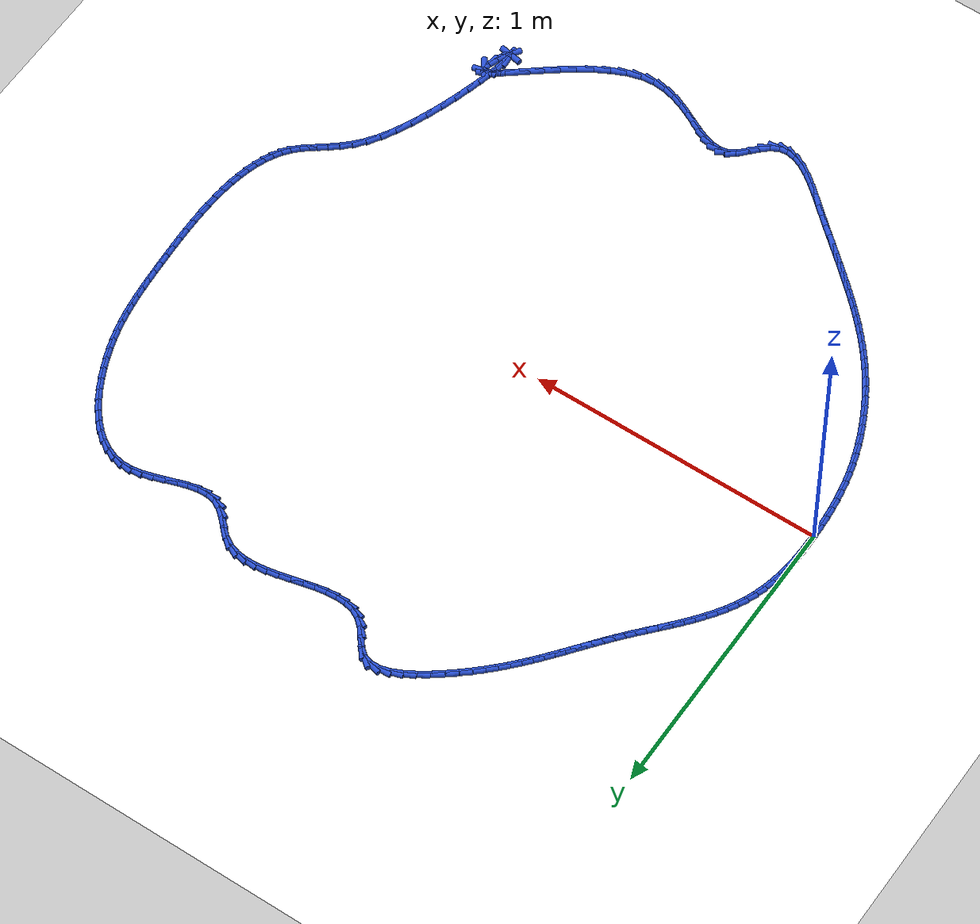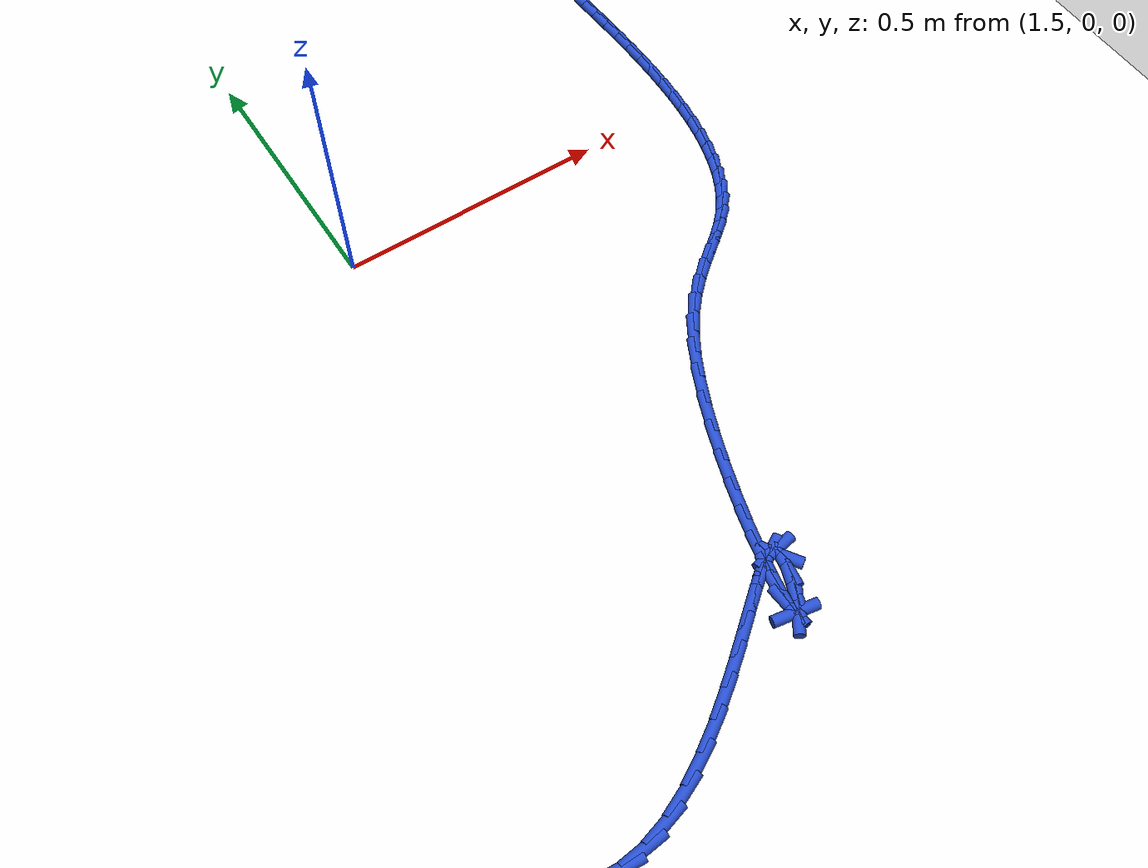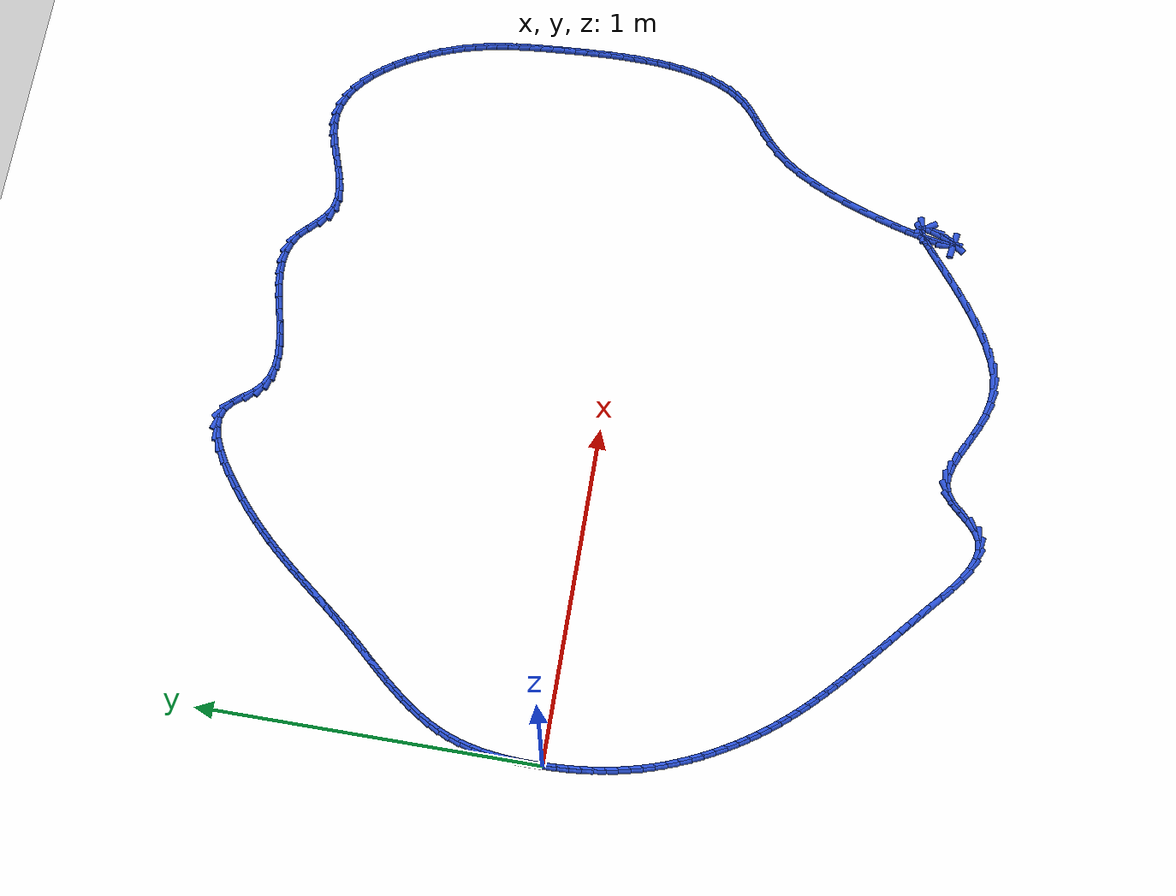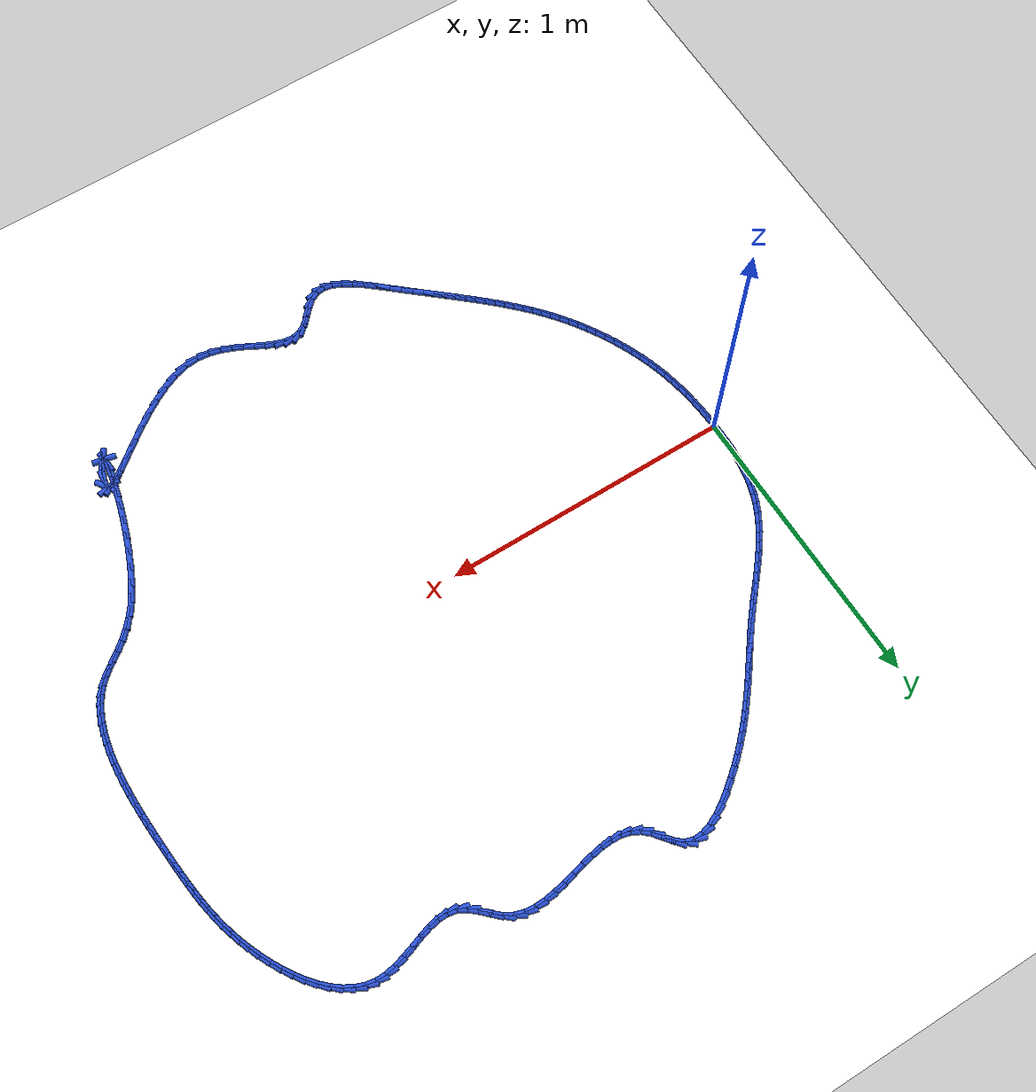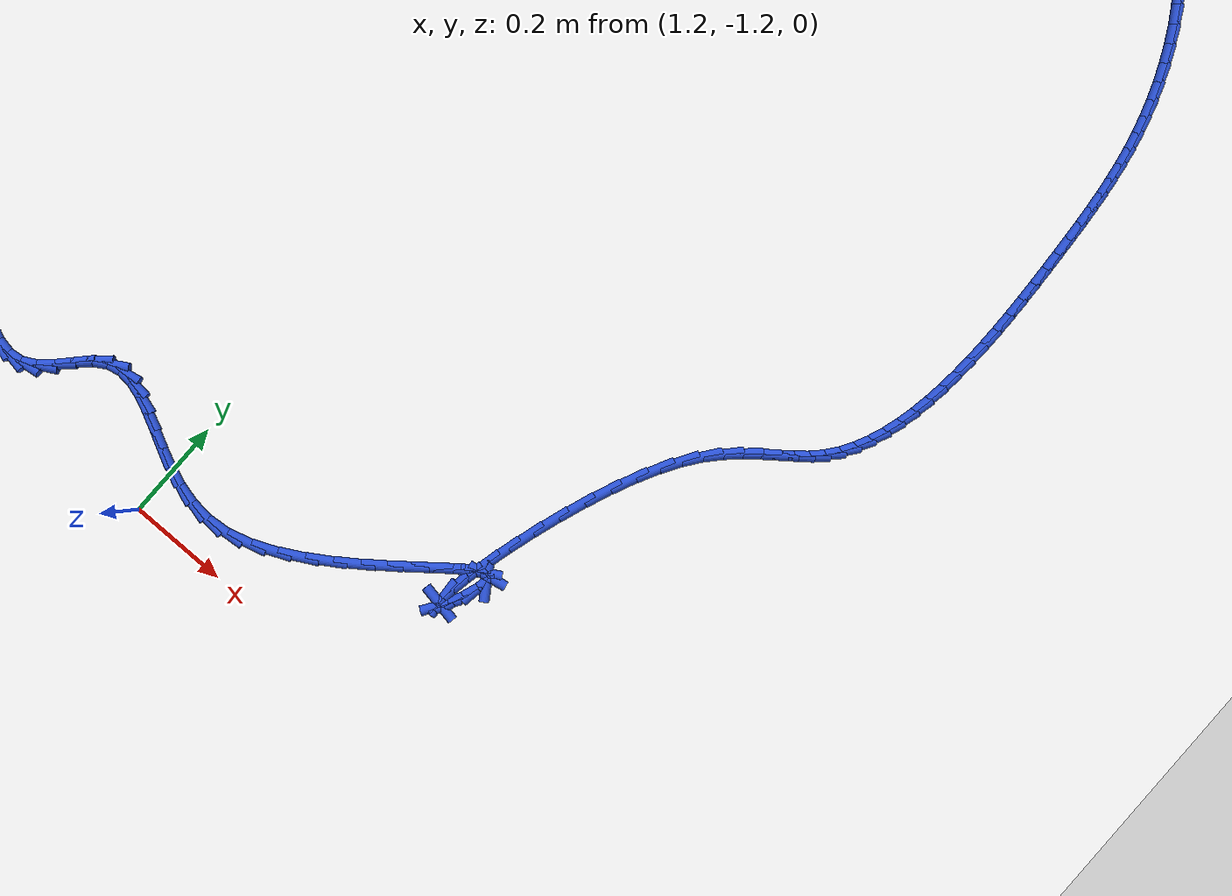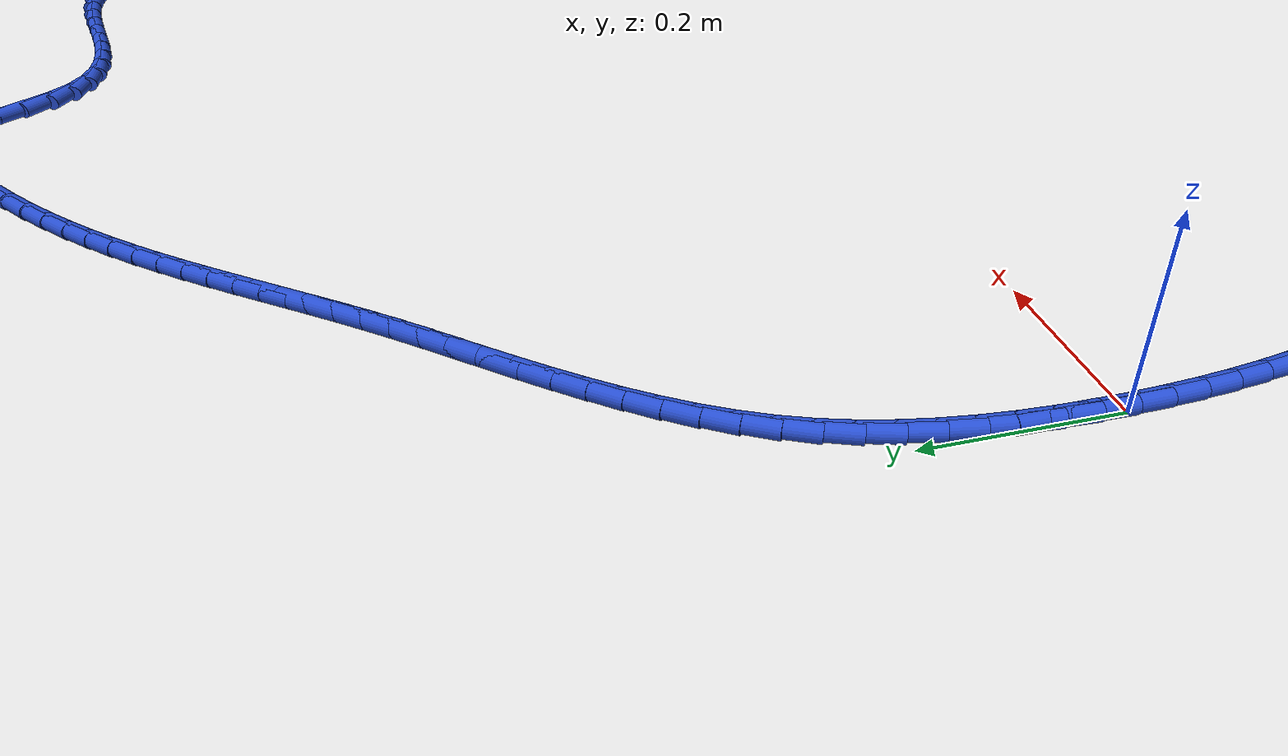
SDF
<sdf version="1.6">
 <world name="default">
  <light name="sun" type="directional">
   <pose>0 0 10 0 -0 0</pose>
   <diffuse>0.8 0.8 0.8 1</diffuse>
   <specular>0.2 0.2 0.2 1</specular>
   <attenuation>
    <range>1000</range>
    <constant>0.9</constant>
    <linear>0.01</linear>
    <quadratic>0.001</quadratic>
   </attenuation>
   <direction>-0.5 0.1 -0.9</direction>
  </light>
  <model name="ground_plane">
   <static>1</static>
   <link name="link">
    <collision name="collision">
     <geometry><plane><normal>0 0 1</normal><size>100 100</size></plane></geometry>
     <surface><friction><ode><mu>100</mu><mu2>50</mu2></ode></friction></surface>
    </collision>
    <visual name="visual">
     <cast_shadows>0</cast_shadows>
     <geometry><plane><normal>0 0 1</normal><size>100 100</size></plane></geometry>
     <material>
      <script><uri>file://media/materials/scripts/gazebo.material</uri><name>Gazebo/WhiteGlow</name></script>
     </material>
    </visual>
   </link>
  </model>
  <gravity>0 0 -9.8</gravity>
  <magnetic_field>6e-06 2.3e-05 -4.2e-05</magnetic_field>
  <atmosphere type="adiabatic"/>
  <physics name="default_physics" default="0" type="ode">
   <max_step_size>0.001</max_step_size>
   <real_time_factor>1</real_time_factor>
   <real_time_update_rate>1000</real_time_update_rate>
  </physics>
  <scene><ambient>0.4 0.4 0.4 1</ambient><background>0.7 0.7 0.7 1</background><shadows>1</shadows></scene>
  <spherical_coordinates>
   <surface_model>EARTH_WGS84</surface_model>
   <latitude_deg>0</latitude_deg>
   <longitude_deg>0</longitude_deg>
   <elevation>0</elevation>
   <heading_deg>0</heading_deg>
  </spherical_coordinates>
  <model name="line">
   <link name="link_0">
    <pose>-7.37257477290143e-18 9.71445146547012e-17 0.01 0 1.57 -1.562745904130109</pose>
    <collision name="collision">
     <geometry><cylinder><radius>0.01</radius><length>0.08</length></cylinder></geometry>
    </collision>
    <visual name="visual">
     <material>
      <script><name>Gazebo/Blue</name><uri>file://media/materials/scripts/gazebo.material</uri></script>
     </material>
     <geometry><cylinder><radius>0.01</radius><length>0.08</length></cylinder></geometry>
    </visual>
   </link>
   <link name="link_1">
    <pose>-0.0002816956772170364 0.034990658679634766 0.01 0 1.57 1.5496413400267557</pose>
    <collision name="collision">
     <geometry><cylinder><radius>0.01</radius><length>0.08</length></cylinder></geometry>
    </collision>
    <visual name="visual">
     <material>
      <script><name>Gazebo/Blue</name><uri>file://media/materials/scripts/gazebo.material</uri></script>
     </material>
     <geometry><cylinder><radius>0.01</radius><length>0.08</length></cylinder></geometry>
    </visual>
   </link>
   <link name="link_2">
    <pose>0.0004599208998079532 0.07004177684413483 0.01 0 1.57 1.515356323330068</pose>
    <collision name="collision">
     <geometry><cylinder><radius>0.01</radius><length>0.08</length></cylinder></geometry>
    </collision>
    <visual name="visual">
     <material>
      <script><name>Gazebo/Blue</name><uri>file://media/materials/scripts/gazebo.material</uri></script>
     </material>
     <geometry><cylinder><radius>0.01</radius><length>0.08</length></cylinder></geometry>
    </visual>
   </link>
   <link name="link_3">
    <pose>0.0024008203007227034 0.10501490743432369 0.01 0 1.57 1.4756737951249999</pose>
    <collision name="collision">
     <geometry><cylinder><radius>0.01</radius><length>0.08</length></cylinder></geometry>
    </collision>
    <visual name="visual">
     <material>
      <script><name>Gazebo/Blue</name><uri>file://media/materials/scripts/gazebo.material</uri></script>
     </material>
     <geometry><cylinder><radius>0.01</radius><length>0.08</length></cylinder></geometry>
    </visual>
   </link>
   <link name="link_4">
    <pose>0.005716973095174958 0.1397716033910247 0.01 0 1.57 1.4302432019320153</pose>
    <collision name="collision">
     <geometry><cylinder><radius>0.01</radius><length>0.08</length></cylinder></geometry>
    </collision>
    <visual name="visual">
     <material>
      <script><name>Gazebo/Blue</name><uri>file://media/materials/scripts/gazebo.material</uri></script>
     </material>
     <geometry><cylinder><radius>0.01</radius><length>0.08</length></cylinder></geometry>
    </visual>
   </link>
   <link name="link_5">
    <pose>0.010584349852812458 0.1741734176550612 0.01 0 1.57 1.3787126563604786</pose>
    <collision name="collision">
     <geometry><cylinder><radius>0.01</radius><length>0.08</length></cylinder></geometry>
    </collision>
    <visual name="visual">
     <material>
      <script><name>Gazebo/Blue</name><uri>file://media/materials/scripts/gazebo.material</uri></script>
     </material>
     <geometry><cylinder><radius>0.01</radius><length>0.08</length></cylinder></geometry>
    </visual>
   </link>
   <link name="link_6">
    <pose>0.017178921143282948 0.20808190316725653 0.01 0 1.57 1.320773830777461</pose>
    <collision name="collision">
     <geometry><cylinder><radius>0.01</radius><length>0.08</length></cylinder></geometry>
    </collision>
    <visual name="visual">
     <material>
      <script><name>Gazebo/Blue</name><uri>file://media/materials/scripts/gazebo.material</uri></script>
     </material>
     <geometry><cylinder><radius>0.01</radius><length>0.08</length></cylinder></geometry>
    </visual>
   </link>
   <link name="link_7">
    <pose>0.025676657536234167 0.24135861286843402 0.01 0 1.57 1.256223234335195</pose>
    <collision name="collision">
     <geometry><cylinder><radius>0.01</radius><length>0.08</length></cylinder></geometry>
    </collision>
    <visual name="visual">
     <material>
      <script><name>Gazebo/Blue</name><uri>file://media/materials/scripts/gazebo.material</uri></script>
     </material>
     <geometry><cylinder><radius>0.01</radius><length>0.08</length></cylinder></geometry>
    </visual>
   </link>
   <link name="link_8">
    <pose>0.03625352960131386 0.27386509969941714 0.01 0 1.57 1.1851395864691066</pose>
    <collision name="collision">
     <geometry><cylinder><radius>0.01</radius><length>0.08</length></cylinder></geometry>
    </collision>
    <visual name="visual">
     <material>
      <script><name>Gazebo/Blue</name><uri>file://media/materials/scripts/gazebo.material</uri></script>
     </material>
     <geometry><cylinder><radius>0.01</radius><length>0.08</length></cylinder></geometry>
    </visual>
   </link>
   <link name="link_9">
    <pose>0.04908243517271146 0.3054644160317214 0.01 0 1.57 1.1134043254828168</pose>
    <collision name="collision">
     <geometry><cylinder><radius>0.01</radius><length>0.08</length></cylinder></geometry>
    </collision>
    <visual name="visual">
     <material>
      <script><name>Gazebo/Blue</name><uri>file://media/materials/scripts/gazebo.material</uri></script>
     </material>
     <geometry><cylinder><radius>0.01</radius><length>0.08</length></cylinder></geometry>
    </visual>
   </link>
   <link name="link_10">
    <pose>0.06416337652792929 0.33610398365550337 0.01 0 1.57 1.0499142067764813</pose>
    <collision name="collision">
     <geometry><cylinder><radius>0.01</radius><length>0.08</length></cylinder></geometry>
    </collision>
    <visual name="visual">
     <material>
      <script><name>Gazebo/Blue</name><uri>file://media/materials/scripts/gazebo.material</uri></script>
     </material>
     <geometry><cylinder><radius>0.01</radius><length>0.08</length></cylinder></geometry>
    </visual>
   </link>
   <link name="link_11">
    <pose>0.08123476214195655 0.36585887666998373 0.01 0 1.57 0.9954628215977714</pose>
    <collision name="collision">
     <geometry><cylinder><radius>0.01</radius><length>0.08</length></cylinder></geometry>
    </collision>
    <visual name="visual">
     <material>
      <script><name>Gazebo/Blue</name><uri>file://media/materials/scripts/gazebo.material</uri></script>
     </material>
     <geometry><cylinder><radius>0.01</radius><length>0.08</length></cylinder></geometry>
    </visual>
   </link>
   <link name="link_12">
    <pose>0.1000132289008868 0.3948147932548004 0.01 0 1.57 0.9498702573837978</pose>
    <collision name="collision">
     <geometry><cylinder><radius>0.01</radius><length>0.08</length></cylinder></geometry>
    </collision>
    <visual name="visual">
     <material>
      <script><name>Gazebo/Blue</name><uri>file://media/materials/scripts/gazebo.material</uri></script>
     </material>
     <geometry><cylinder><radius>0.01</radius><length>0.08</length></cylinder></geometry>
    </visual>
   </link>
   <link name="link_13">
    <pose>0.1202154136908138 0.42305743158959125 0.01 0 1.57 0.9128253980258968</pose>
    <collision name="collision">
     <geometry><cylinder><radius>0.01</radius><length>0.08</length></cylinder></geometry>
    </collision>
    <visual name="visual">
     <material>
      <script><name>Gazebo/Blue</name><uri>file://media/materials/scripts/gazebo.material</uri></script>
     </material>
     <geometry><cylinder><radius>0.01</radius><length>0.08</length></cylinder></geometry>
    </visual>
   </link>
   <link name="link_14">
    <pose>0.14155795339783128 0.4506724898539948 0.01 0 1.57 0.8839891264557248</pose>
    <collision name="collision">
     <geometry><cylinder><radius>0.01</radius><length>0.08</length></cylinder></geometry>
    </collision>
    <visual name="visual">
     <material>
      <script><name>Gazebo/Blue</name><uri>file://media/materials/scripts/gazebo.material</uri></script>
     </material>
     <geometry><cylinder><radius>0.01</radius><length>0.08</length></cylinder></geometry>
    </visual>
   </link>
   <link name="link_15">
    <pose>0.16375748490803274 0.4777456662276481 0.01 0 1.57 0.863067492049185</pose>
    <collision name="collision">
     <geometry><cylinder><radius>0.01</radius><length>0.08</length></cylinder></geometry>
    </collision>
    <visual name="visual">
     <material>
      <script><name>Gazebo/Blue</name><uri>file://media/materials/scripts/gazebo.material</uri></script>
     </material>
     <geometry><cylinder><radius>0.01</radius><length>0.08</length></cylinder></geometry>
    </visual>
   </link>
   <link name="link_16">
    <pose>0.18653064510751188 0.5043626588901896 0.01 0 1.57 0.8498612615660565</pose>
    <collision name="collision">
     <geometry><cylinder><radius>0.01</radius><length>0.08</length></cylinder></geometry>
    </collision>
    <visual name="visual">
     <material>
      <script><name>Gazebo/Blue</name><uri>file://media/materials/scripts/gazebo.material</uri></script>
     </material>
     <geometry><cylinder><radius>0.01</radius><length>0.08</length></cylinder></geometry>
    </visual>
   </link>
   <link name="link_17">
    <pose>0.20959407088236234 0.530609166021257 0.01 0 1.57 0.8442993746222155</pose>
    <collision name="collision">
     <geometry><cylinder><radius>0.01</radius><length>0.08</length></cylinder></geometry>
    </collision>
    <visual name="visual">
     <material>
      <script><name>Gazebo/Blue</name><uri>file://media/materials/scripts/gazebo.material</uri></script>
     </material>
     <geometry><cylinder><radius>0.01</radius><length>0.08</length></cylinder></geometry>
    </visual>
   </link>
   <link name="link_18">
    <pose>0.23266439911867784 0.5565708858004882 0.01 0 1.57 0.8464625355110619</pose>
    <collision name="collision">
     <geometry><cylinder><radius>0.01</radius><length>0.08</length></cylinder></geometry>
    </collision>
    <visual name="visual">
     <material>
      <script><name>Gazebo/Blue</name><uri>file://media/materials/scripts/gazebo.material</uri></script>
     </material>
     <geometry><cylinder><radius>0.01</radius><length>0.08</length></cylinder></geometry>
    </visual>
   </link>
   <link name="link_19">
    <pose>0.2554582667025522 0.5823335164075215 0.01 0 1.57 0.856600932061387</pose>
    <collision name="collision">
     <geometry><cylinder><radius>0.01</radius><length>0.08</length></cylinder></geometry>
    </collision>
    <visual name="visual">
     <material>
      <script><name>Gazebo/Blue</name><uri>file://media/materials/scripts/gazebo.material</uri></script>
     </material>
     <geometry><cylinder><radius>0.01</radius><length>0.08</length></cylinder></geometry>
    </visual>
   </link>
   <link name="link_20">
    <pose>0.2776923105200786 0.6079827560219941 0.01 0 1.57 0.8732345664060137</pose>
    <collision name="collision">
     <geometry><cylinder><radius>0.01</radius><length>0.08</length></cylinder></geometry>
    </collision>
    <visual name="visual">
     <material>
      <script><name>Gazebo/Blue</name><uri>file://media/materials/scripts/gazebo.material</uri></script>
     </material>
     <geometry><cylinder><radius>0.01</radius><length>0.08</length></cylinder></geometry>
    </visual>
   </link>
   <link name="link_21">
    <pose>0.2991556727107114 0.6335914219990036 0.01 0 1.57 0.8883167888411567</pose>
    <collision name="collision">
     <geometry><cylinder><radius>0.01</radius><length>0.08</length></cylinder></geometry>
    </collision>
    <visual name="visual">
     <material>
      <script><name>Gazebo/Blue</name><uri>file://media/materials/scripts/gazebo.material</uri></script>
     </material>
     <geometry><cylinder><radius>0.01</radius><length>0.08</length></cylinder></geometry>
    </visual>
   </link>
   <link name="link_22">
    <pose>0.3199506357465388 0.6591767011635202 0.01 0 1.57 0.8993529324511338</pose>
    <collision name="collision">
     <geometry><cylinder><radius>0.01</radius><length>0.08</length></cylinder></geometry>
    </collision>
    <visual name="visual">
     <material>
      <script><name>Gazebo/Blue</name><uri>file://media/materials/scripts/gazebo.material</uri></script>
     </material>
     <geometry><cylinder><radius>0.01</radius><length>0.08</length></cylinder></geometry>
    </visual>
   </link>
   <link name="link_23">
    <pose>0.34026400043450217 0.6847407653479269 0.01 0 1.57 0.9060995472290491</pose>
    <collision name="collision">
     <geometry><cylinder><radius>0.01</radius><length>0.08</length></cylinder></geometry>
    </collision>
    <visual name="visual">
     <material>
      <script><name>Gazebo/Blue</name><uri>file://media/materials/scripts/gazebo.material</uri></script>
     </material>
     <geometry><cylinder><radius>0.01</radius><length>0.08</length></cylinder></geometry>
    </visual>
   </link>
   <link name="link_24">
    <pose>0.36028256888950366 0.7102857861522435 0.01 0 1.57 0.908403689949582</pose>
    <collision name="collision">
     <geometry><cylinder><radius>0.01</radius><length>0.08</length></cylinder></geometry>
    </collision>
    <visual name="visual">
     <material>
      <script><name>Gazebo/Blue</name><uri>file://media/materials/scripts/gazebo.material</uri></script>
     </material>
     <geometry><cylinder><radius>0.01</radius><length>0.08</length></cylinder></geometry>
    </visual>
   </link>
   <link name="link_25">
    <pose>0.38019314322644554 0.7358139351764884 0.01 0 1.57 0.9062074800982112</pose>
    <collision name="collision">
     <geometry><cylinder><radius>0.01</radius><length>0.08</length></cylinder></geometry>
    </collision>
    <visual name="visual">
     <material>
      <script><name>Gazebo/Blue</name><uri>file://media/materials/scripts/gazebo.material</uri></script>
     </material>
     <geometry><cylinder><radius>0.01</radius><length>0.08</length></cylinder></geometry>
    </visual>
   </link>
   <link name="link_26">
    <pose>0.4001825255602298 0.7613273840206815 0.01 0 1.57 0.8995500128478302</pose>
    <collision name="collision">
     <geometry><cylinder><radius>0.01</radius><length>0.08</length></cylinder></geometry>
    </collision>
    <visual name="visual">
     <material>
      <script><name>Gazebo/Blue</name><uri>file://media/materials/scripts/gazebo.material</uri></script>
     </material>
     <geometry><cylinder><radius>0.01</radius><length>0.08</length></cylinder></geometry>
    </visual>
   </link>
   <link name="link_27">
    <pose>0.4204375180057587 0.7868283042848415 0.01 0 1.57 0.8885666906850642</pose>
    <collision name="collision">
     <geometry><cylinder><radius>0.01</radius><length>0.08</length></cylinder></geometry>
    </collision>
    <visual name="visual">
     <material>
      <script><name>Gazebo/Blue</name><uri>file://media/materials/scripts/gazebo.material</uri></script>
     </material>
     <geometry><cylinder><radius>0.01</radius><length>0.08</length></cylinder></geometry>
    </visual>
   </link>
   <link name="link_28">
    <pose>0.4411449226779342 0.8123188675689879 0.01 0 1.57 0.8734858136725207</pose>
    <collision name="collision">
     <geometry><cylinder><radius>0.01</radius><length>0.08</length></cylinder></geometry>
    </collision>
    <visual name="visual">
     <material>
      <script><name>Gazebo/Blue</name><uri>file://media/materials/scripts/gazebo.material</uri></script>
     </material>
     <geometry><cylinder><radius>0.01</radius><length>0.08</length></cylinder></geometry>
    </visual>
   </link>
   <link name="link_29">
    <pose>0.4624915416916584 0.8378012454731395 0.01 0 1.57 0.8546220693673238</pose>
    <collision name="collision">
     <geometry><cylinder><radius>0.01</radius><length>0.08</length></cylinder></geometry>
    </collision>
    <visual name="visual">
     <material>
      <script><name>Gazebo/Blue</name><uri>file://media/materials/scripts/gazebo.material</uri></script>
     </material>
     <geometry><cylinder><radius>0.01</radius><length>0.08</length></cylinder></geometry>
    </visual>
   </link>
   <link name="link_30">
    <pose>0.48466417716183396 0.8632776095973161 0.01 0 1.57 0.8323665345735363</pose>
    <collision name="collision">
     <geometry><cylinder><radius>0.01</radius><length>0.08</length></cylinder></geometry>
    </collision>
    <visual name="visual">
     <material>
      <script><name>Gazebo/Blue</name><uri>file://media/materials/scripts/gazebo.material</uri></script>
     </material>
     <geometry><cylinder><radius>0.01</radius><length>0.08</length></cylinder></geometry>
    </visual>
   </link>
   <link name="link_31">
    <pose>0.5078496312033622 0.8887501315415361 0.01 0 1.57 0.8071730076617267</pose>
    <collision name="collision">
     <geometry><cylinder><radius>0.01</radius><length>0.08</length></cylinder></geometry>
    </collision>
    <visual name="visual">
     <material>
      <script><name>Gazebo/Blue</name><uri>file://media/materials/scripts/gazebo.material</uri></script>
     </material>
     <geometry><cylinder><radius>0.01</radius><length>0.08</length></cylinder></geometry>
    </visual>
   </link>
   <link name="link_32">
    <pose>0.5322347059311461 0.9142209829058197 0.01 0 1.57 0.7795409225787113</pose>
    <collision name="collision">
     <geometry><cylinder><radius>0.01</radius><length>0.08</length></cylinder></geometry>
    </collision>
    <visual name="visual">
     <material>
      <script><name>Gazebo/Blue</name><uri>file://media/materials/scripts/gazebo.material</uri></script>
     </material>
     <geometry><cylinder><radius>0.01</radius><length>0.08</length></cylinder></geometry>
    </visual>
   </link>
   <link name="link_33">
    <pose>0.5580062034600871 0.9396923352901854 0.01 0 1.57 0.7499956609281561</pose>
    <collision name="collision">
     <geometry><cylinder><radius>0.01</radius><length>0.08</length></cylinder></geometry>
    </collision>
    <visual name="visual">
     <material>
      <script><name>Gazebo/Blue</name><uri>file://media/materials/scripts/gazebo.material</uri></script>
     </material>
     <geometry><cylinder><radius>0.01</radius><length>0.08</length></cylinder></geometry>
    </visual>
   </link>
   <link name="link_34">
    <pose>0.5853509259050875 0.9651663602946523 0.01 0 1.57 0.7190676207797878</pose>
    <collision name="collision">
     <geometry><cylinder><radius>0.01</radius><length>0.08</length></cylinder></geometry>
    </collision>
    <visual name="visual">
     <material>
      <script><name>Gazebo/Blue</name><uri>file://media/materials/scripts/gazebo.material</uri></script>
     </material>
     <geometry><cylinder><radius>0.01</radius><length>0.08</length></cylinder></geometry>
    </visual>
   </link>
   <link name="link_35">
    <pose>0.6144556753810498 0.9906452295192398 0.01 0 1.57 0.6872717512260096</pose>
    <collision name="collision">
     <geometry><cylinder><radius>0.01</radius><length>0.08</length></cylinder></geometry>
    </collision>
    <visual name="visual">
     <material>
      <script><name>Gazebo/Blue</name><uri>file://media/materials/scripts/gazebo.material</uri></script>
     </material>
     <geometry><cylinder><radius>0.01</radius><length>0.08</length></cylinder></geometry>
    </visual>
   </link>
   <link name="link_36">
    <pose>0.6455072540028757 1.0161311145639673 0.01 0 1.57 0.6538108150438107</pose>
    <collision name="collision">
     <geometry><cylinder><radius>0.01</radius><length>0.08</length></cylinder></geometry>
    </collision>
    <visual name="visual">
     <material>
      <script><name>Gazebo/Blue</name><uri>file://media/materials/scripts/gazebo.material</uri></script>
     </material>
     <geometry><cylinder><radius>0.01</radius><length>0.08</length></cylinder></geometry>
    </visual>
   </link>
   <link name="link_37">
    <pose>0.6786090806369028 1.0414948935218273 0.01 0 1.57 0.6074932444940689</pose>
    <collision name="collision">
     <geometry><cylinder><radius>0.01</radius><length>0.08</length></cylinder></geometry>
    </collision>
    <visual name="visual">
     <material>
      <script><name>Gazebo/Blue</name><uri>file://media/materials/scripts/gazebo.material</uri></script>
     </material>
     <geometry><cylinder><radius>0.01</radius><length>0.08</length></cylinder></geometry>
    </visual>
   </link>
   <link name="link_38">
    <pose>0.7131787086998016 1.0655274951940188 0.01 0 1.57 0.5381341451157671</pose>
    <collision name="collision">
     <geometry><cylinder><radius>0.01</radius><length>0.08</length></cylinder></geometry>
    </collision>
    <visual name="visual">
     <material>
      <script><name>Gazebo/Blue</name><uri>file://media/materials/scripts/gazebo.material</uri></script>
     </material>
     <geometry><cylinder><radius>0.01</radius><length>0.08</length></cylinder></geometry>
    </visual>
   </link>
   <link name="link_39">
    <pose>0.748296762517281 1.0864893269312939 0.01 0 1.57 0.4350559094443323</pose>
    <collision name="collision">
     <geometry><cylinder><radius>0.01</radius><length>0.08</length></cylinder></geometry>
    </collision>
    <visual name="visual">
     <material>
      <script><name>Gazebo/Blue</name><uri>file://media/materials/scripts/gazebo.material</uri></script>
     </material>
     <geometry><cylinder><radius>0.01</radius><length>0.08</length></cylinder></geometry>
    </visual>
   </link>
   <link name="link_40">
    <pose>0.7830415312503389 1.1026371191832327 0.01 0 1.57 0.27922271353270145</pose>
    <collision name="collision">
     <geometry><cylinder><radius>0.01</radius><length>0.08</length></cylinder></geometry>
    </collision>
    <visual name="visual">
     <material>
      <script><name>Gazebo/Blue</name><uri>file://media/materials/scripts/gazebo.material</uri></script>
     </material>
     <geometry><cylinder><radius>0.01</radius><length>0.08</length></cylinder></geometry>
    </visual>
   </link>
   <link name="link_41">
    <pose>0.8164913040599725 1.1122276023994127 0.01 0 1.57 0.041275871189068454</pose>
    <collision name="collision">
     <geometry><cylinder><radius>0.01</radius><length>0.08</length></cylinder></geometry>
    </collision>
    <visual name="visual">
     <material>
      <script><name>Gazebo/Blue</name><uri>file://media/materials/scripts/gazebo.material</uri></script>
     </material>
     <geometry><cylinder><radius>0.01</radius><length>0.08</length></cylinder></geometry>
    </visual>
   </link>
   <link name="link_42">
    <pose>0.8477243701071794 1.1135175070294143 0.01 0 1.57 -0.3020534082997455</pose>
    <collision name="collision">
     <geometry><cylinder><radius>0.01</radius><length>0.08</length></cylinder></geometry>
    </collision>
    <visual name="visual">
     <material>
      <script><name>Gazebo/Blue</name><uri>file://media/materials/scripts/gazebo.material</uri></script>
     </material>
     <geometry><cylinder><radius>0.01</radius><length>0.08</length></cylinder></geometry>
    </visual>
   </link>
   <link name="link_43">
    <pose>0.8758190185529571 1.1047635635228157 0.01 0 1.57 -0.6909817485402148</pose>
    <collision name="collision">
     <geometry><cylinder><radius>0.01</radius><length>0.08</length></cylinder></geometry>
    </collision>
    <visual name="visual">
     <material>
      <script><name>Gazebo/Blue</name><uri>file://media/materials/scripts/gazebo.material</uri></script>
     </material>
     <geometry><cylinder><radius>0.01</radius><length>0.08</length></cylinder></geometry>
    </visual>
   </link>
   <link name="link_44">
    <pose>0.9000581085399401 1.0847181284284804 0.01 0 1.57 -0.9024392311679303</pose>
    <collision name="collision">
     <geometry><cylinder><radius>0.01</radius><length>0.08</length></cylinder></geometry>
    </collision>
    <visual name="visual">
     <material>
      <script><name>Gazebo/Blue</name><uri>file://media/materials/scripts/gazebo.material</uri></script>
     </material>
     <geometry><cylinder><radius>0.01</radius><length>0.08</length></cylinder></geometry>
    </visual>
   </link>
   <link name="link_45">
    <pose>0.9218054783194697 1.057175292913835 0.01 0 1.57 -0.9137761795977895</pose>
    <collision name="collision">
     <geometry><cylinder><radius>0.01</radius><length>0.08</length></cylinder></geometry>
    </collision>
    <visual name="visual">
     <material>
      <script><name>Gazebo/Blue</name><uri>file://media/materials/scripts/gazebo.material</uri></script>
     </material>
     <geometry><cylinder><radius>0.01</radius><length>0.08</length></cylinder></geometry>
    </visual>
   </link>
   <link name="link_46">
    <pose>0.9436387041290661 1.0288697566306404 0.01 0 1.57 -0.7461342841469327</pose>
    <collision name="collision">
     <geometry><cylinder><radius>0.01</radius><length>0.08</length></cylinder></geometry>
    </collision>
    <visual name="visual">
     <material>
      <script><name>Gazebo/Blue</name><uri>file://media/materials/scripts/gazebo.material</uri></script>
     </material>
     <geometry><cylinder><radius>0.01</radius><length>0.08</length></cylinder></geometry>
    </visual>
   </link>
   <link name="link_47">
    <pose>0.9680474332112358 1.0063062866474355 0.01 0 1.57 -0.4812787876785755</pose>
    <collision name="collision">
     <geometry><cylinder><radius>0.01</radius><length>0.08</length></cylinder></geometry>
    </collision>
    <visual name="visual">
     <material>
      <script><name>Gazebo/Blue</name><uri>file://media/materials/scripts/gazebo.material</uri></script>
     </material>
     <geometry><cylinder><radius>0.01</radius><length>0.08</length></cylinder></geometry>
    </visual>
   </link>
   <link name="link_48">
    <pose>0.995888700539336 0.9917665380177938 0.01 0 1.57 -0.24199416337558027</pose>
    <collision name="collision">
     <geometry><cylinder><radius>0.01</radius><length>0.08</length></cylinder></geometry>
    </collision>
    <visual name="visual">
     <material>
      <script><name>Gazebo/Blue</name><uri>file://media/materials/scripts/gazebo.material</uri></script>
     </material>
     <geometry><cylinder><radius>0.01</radius><length>0.08</length></cylinder></geometry>
    </visual>
   </link>
   <link name="link_49">
    <pose>1.0267149856721542 0.9841576452495602 0.01 0 1.57 -0.055906371077151774</pose>
    <collision name="collision">
     <geometry><cylinder><radius>0.01</radius><length>0.08</length></cylinder></geometry>
    </collision>
    <visual name="visual">
     <material>
      <script><name>Gazebo/Blue</name><uri>file://media/materials/scripts/gazebo.material</uri></script>
     </material>
     <geometry><cylinder><radius>0.01</radius><length>0.08</length></cylinder></geometry>
    </visual>
   </link>
   <link name="link_50">
    <pose>1.0600423312438287 0.9822924907019327 0.01 0 1.57 0.07600293029042648</pose>
    <collision name="collision">
     <geometry><cylinder><radius>0.01</radius><length>0.08</length></cylinder></geometry>
    </collision>
    <visual name="visual">
     <material>
      <script><name>Gazebo/Blue</name><uri>file://media/materials/scripts/gazebo.material</uri></script>
     </material>
     <geometry><cylinder><radius>0.01</radius><length>0.08</length></cylinder></geometry>
    </visual>
   </link>
   <link name="link_51">
    <pose>1.0953867798884975 0.9849839567341087 0.01 0 1.57 0.16289737991464598</pose>
    <collision name="collision">
     <geometry><cylinder><radius>0.01</radius><length>0.08</length></cylinder></geometry>
    </collision>
    <visual name="visual">
     <material>
      <script><name>Gazebo/Blue</name><uri>file://media/materials/scripts/gazebo.material</uri></script>
     </material>
     <geometry><cylinder><radius>0.01</radius><length>0.08</length></cylinder></geometry>
    </visual>
   </link>
   <link name="link_52">
    <pose>1.1322643742402994 0.9910449257052864 0.01 0 1.57 0.21402043840707194</pose>
    <collision name="collision">
     <geometry><cylinder><radius>0.01</radius><length>0.08</length></cylinder></geometry>
    </collision>
    <visual name="visual">
     <material>
      <script><name>Gazebo/Blue</name><uri>file://media/materials/scripts/gazebo.material</uri></script>
     </material>
     <geometry><cylinder><radius>0.01</radius><length>0.08</length></cylinder></geometry>
    </visual>
   </link>
   <link name="link_53">
    <pose>1.1701911569333727 0.9992882799746642 0.01 0 1.57 0.23555821225678733</pose>
    <collision name="collision">
     <geometry><cylinder><radius>0.01</radius><length>0.08</length></cylinder></geometry>
    </collision>
    <visual name="visual">
     <material>
      <script><name>Gazebo/Blue</name><uri>file://media/materials/scripts/gazebo.material</uri></script>
     </material>
     <geometry><cylinder><radius>0.01</radius><length>0.08</length></cylinder></geometry>
    </visual>
   </link>
   <link name="link_54">
    <pose>1.2086831706018553 1.0085269019014396 0.01 0 1.57 0.23037090674319213</pose>
    <collision name="collision">
     <geometry><cylinder><radius>0.01</radius><length>0.08</length></cylinder></geometry>
    </collision>
    <visual name="visual">
     <material>
      <script><name>Gazebo/Blue</name><uri>file://media/materials/scripts/gazebo.material</uri></script>
     </material>
     <geometry><cylinder><radius>0.01</radius><length>0.08</length></cylinder></geometry>
    </visual>
   </link>
   <link name="link_55">
    <pose>1.247256457879886 1.017573673844811 0.01 0 1.57 0.19824392442982408</pose>
    <collision name="collision">
     <geometry><cylinder><radius>0.01</radius><length>0.08</length></cylinder></geometry>
    </collision>
    <visual name="visual">
     <material>
      <script><name>Gazebo/Blue</name><uri>file://media/materials/scripts/gazebo.material</uri></script>
     </material>
     <geometry><cylinder><radius>0.01</radius><length>0.08</length></cylinder></geometry>
    </visual>
   </link>
   <link name="link_56">
    <pose>1.2854270614016032 1.0252414781639763 0.01 0 1.57 0.13598960242928598</pose>
    <collision name="collision">
     <geometry><cylinder><radius>0.01</radius><length>0.08</length></cylinder></geometry>
    </collision>
    <visual name="visual">
     <material>
      <script><name>Gazebo/Blue</name><uri>file://media/materials/scripts/gazebo.material</uri></script>
     </material>
     <geometry><cylinder><radius>0.01</radius><length>0.08</length></cylinder></geometry>
    </visual>
   </link>
   <link name="link_57">
    <pose>1.3227110238011446 1.0303431972181332 0.01 0 1.57 0.03753151368361002</pose>
    <collision name="collision">
     <geometry><cylinder><radius>0.01</radius><length>0.08</length></cylinder></geometry>
    </collision>
    <visual name="visual">
     <material>
      <script><name>Gazebo/Blue</name><uri>file://media/materials/scripts/gazebo.material</uri></script>
     </material>
     <geometry><cylinder><radius>0.01</radius><length>0.08</length></cylinder></geometry>
    </visual>
   </link>
   <link name="link_58">
    <pose>1.3586243877126483 1.0316917133664794 0.01 0 1.57 -0.10507053075840908</pose>
    <collision name="collision">
     <geometry><cylinder><radius>0.01</radius><length>0.08</length></cylinder></geometry>
    </collision>
    <visual name="visual">
     <material>
      <script><name>Gazebo/Blue</name><uri>file://media/materials/scripts/gazebo.material</uri></script>
     </material>
     <geometry><cylinder><radius>0.01</radius><length>0.08</length></cylinder></geometry>
    </visual>
   </link>
   <link name="link_59">
    <pose>1.3926831957702541 1.028099908968214 0.01 0 1.57 -0.29732211980720374</pose>
    <collision name="collision">
     <geometry><cylinder><radius>0.01</radius><length>0.08</length></cylinder></geometry>
    </collision>
    <visual name="visual">
     <material>
      <script><name>Gazebo/Blue</name><uri>file://media/materials/scripts/gazebo.material</uri></script>
     </material>
     <geometry><cylinder><radius>0.01</radius><length>0.08</length></cylinder></geometry>
    </visual>
   </link>
   <link name="link_60">
    <pose>1.4244034906080993 1.0183806663825337 0.01 0 1.57 -0.5316618850577869</pose>
    <collision name="collision">
     <geometry><cylinder><radius>0.01</radius><length>0.08</length></cylinder></geometry>
    </collision>
    <visual name="visual">
     <material>
      <script><name>Gazebo/Blue</name><uri>file://media/materials/scripts/gazebo.material</uri></script>
     </material>
     <geometry><cylinder><radius>0.01</radius><length>0.08</length></cylinder></geometry>
    </visual>
   </link>
   <link name="link_61">
    <pose>1.4533120705243034 1.0013780388902505 0.01 0 1.57 -0.7247638343255108</pose>
    <collision name="collision">
     <geometry><cylinder><radius>0.01</radius><length>0.08</length></cylinder></geometry>
    </collision>
    <visual name="visual">
     <material>
      <script><name>Gazebo/Blue</name><uri>file://media/materials/scripts/gazebo.material</uri></script>
     </material>
     <geometry><cylinder><radius>0.01</radius><length>0.08</length></cylinder></geometry>
    </visual>
   </link>
   <link name="link_62">
    <pose>1.479662917902621 0.9780435273618503 0.01 0 1.57 -0.786984152612401</pose>
    <collision name="collision">
     <geometry><cylinder><radius>0.01</radius><length>0.08</length></cylinder></geometry>
    </collision>
    <visual name="visual">
     <material>
      <script><name>Gazebo/Blue</name><uri>file://media/materials/scripts/gazebo.material</uri></script>
     </material>
     <geometry><cylinder><radius>0.01</radius><length>0.08</length></cylinder></geometry>
    </visual>
   </link>
   <link name="link_63">
    <pose>1.5048869135632463 0.952739394567252 0.01 0 1.57 -0.7225662436019631</pose>
    <collision name="collision">
     <geometry><cylinder><radius>0.01</radius><length>0.08</length></cylinder></geometry>
    </collision>
    <visual name="visual">
     <material>
      <script><name>Gazebo/Blue</name><uri>file://media/materials/scripts/gazebo.material</uri></script>
     </material>
     <geometry><cylinder><radius>0.01</radius><length>0.08</length></cylinder></geometry>
    </visual>
   </link>
   <link name="link_64">
    <pose>1.5305222250842159 0.9301388303493002 0.01 0 1.57 -0.5069591283011272</pose>
    <collision name="collision">
     <geometry><cylinder><radius>0.01</radius><length>0.08</length></cylinder></geometry>
    </collision>
    <visual name="visual">
     <material>
      <script><name>Gazebo/Blue</name><uri>file://media/materials/scripts/gazebo.material</uri></script>
     </material>
     <geometry><cylinder><radius>0.01</radius><length>0.08</length></cylinder></geometry>
    </visual>
   </link>
   <link name="link_65">
    <pose>1.5580817522650356 0.914833008202309 0.01 0 1.57 -0.20396473009154428</pose>
    <collision name="collision">
     <geometry><cylinder><radius>0.01</radius><length>0.08</length></cylinder></geometry>
    </collision>
    <visual name="visual">
     <material>
      <script><name>Gazebo/Blue</name><uri>file://media/materials/scripts/gazebo.material</uri></script>
     </material>
     <geometry><cylinder><radius>0.01</radius><length>0.08</length></cylinder></geometry>
    </visual>
   </link>
   <link name="link_66">
    <pose>1.5882119869903417 0.9086008396156323 0.01 0 1.57 0.03625475321395188</pose>
    <collision name="collision">
     <geometry><cylinder><radius>0.01</radius><length>0.08</length></cylinder></geometry>
    </collision>
    <visual name="visual">
     <material>
      <script><name>Gazebo/Blue</name><uri>file://media/materials/scripts/gazebo.material</uri></script>
     </material>
     <geometry><cylinder><radius>0.01</radius><length>0.08</length></cylinder></geometry>
    </visual>
   </link>
   <link name="link_67">
    <pose>1.620496719772007 0.9097718277318828 0.01 0 1.57 0.1945889978544093</pose>
    <collision name="collision">
     <geometry><cylinder><radius>0.01</radius><length>0.08</length></cylinder></geometry>
    </collision>
    <visual name="visual">
     <material>
      <script><name>Gazebo/Blue</name><uri>file://media/materials/scripts/gazebo.material</uri></script>
     </material>
     <geometry><cylinder><radius>0.01</radius><length>0.08</length></cylinder></geometry>
    </visual>
   </link>
   <link name="link_68">
    <pose>1.6544547007094565 0.916464361878136 0.01 0 1.57 0.2859006213275771</pose>
    <collision name="collision">
     <geometry><cylinder><radius>0.01</radius><length>0.08</length></cylinder></geometry>
    </collision>
    <visual name="visual">
     <material>
      <script><name>Gazebo/Blue</name><uri>file://media/materials/scripts/gazebo.material</uri></script>
     </material>
     <geometry><cylinder><radius>0.01</radius><length>0.08</length></cylinder></geometry>
    </visual>
   </link>
   <link name="link_69">
    <pose>1.6896046799021138 0.9267968313814663 0.01 0 1.57 0.32519037349739477</pose>
    <collision name="collision">
     <geometry><cylinder><radius>0.01</radius><length>0.08</length></cylinder></geometry>
    </collision>
    <visual name="visual">
     <material>
      <script><name>Gazebo/Blue</name><uri>file://media/materials/scripts/gazebo.material</uri></script>
     </material>
     <geometry><cylinder><radius>0.01</radius><length>0.08</length></cylinder></geometry>
    </visual>
   </link>
   <link name="link_70">
    <pose>1.725465407449402 0.9388876255689487 0.01 0 1.57 0.32018947585189433</pose>
    <collision name="collision">
     <geometry><cylinder><radius>0.01</radius><length>0.08</length></cylinder></geometry>
    </collision>
    <visual name="visual">
     <material>
      <script><name>Gazebo/Blue</name><uri>file://media/materials/scripts/gazebo.material</uri></script>
     </material>
     <geometry><cylinder><radius>0.01</radius><length>0.08</length></cylinder></geometry>
    </visual>
   </link>
   <link name="link_71">
    <pose>1.7615556334507454 0.9508551337676583 0.01 0 1.57 0.271140595921244</pose>
    <collision name="collision">
     <geometry><cylinder><radius>0.01</radius><length>0.08</length></cylinder></geometry>
    </collision>
    <visual name="visual">
     <material>
      <script><name>Gazebo/Blue</name><uri>file://media/materials/scripts/gazebo.material</uri></script>
     </material>
     <geometry><cylinder><radius>0.01</radius><length>0.08</length></cylinder></geometry>
    </visual>
   </link>
   <link name="link_72">
    <pose>1.7973941080055675 0.96081774530467 0.01 0 1.57 0.17138346623998035</pose>
    <collision name="collision">
     <geometry><cylinder><radius>0.01</radius><length>0.08</length></cylinder></geometry>
    </collision>
    <visual name="visual">
     <material>
      <script><name>Gazebo/Blue</name><uri>file://media/materials/scripts/gazebo.material</uri></script>
     </material>
     <geometry><cylinder><radius>0.01</radius><length>0.08</length></cylinder></geometry>
    </visual>
   </link>
   <link name="link_73">
    <pose>1.8324995812132931 0.9668938495070588 0.01 0 1.57 0.010245570493948333</pose>
    <collision name="collision">
     <geometry><cylinder><radius>0.01</radius><length>0.08</length></cylinder></geometry>
    </collision>
    <visual name="visual">
     <material>
      <script><name>Gazebo/Blue</name><uri>file://media/materials/scripts/gazebo.material</uri></script>
     </material>
     <geometry><cylinder><radius>0.01</radius><length>0.08</length></cylinder></geometry>
    </visual>
   </link>
   <link name="link_74">
    <pose>1.8663974870061282 0.9672411650433107 0.01 0 1.57 -0.18547528835380575</pose>
    <collision name="collision">
     <geometry><cylinder><radius>0.01</radius><length>0.08</length></cylinder></geometry>
    </collision>
    <visual name="visual">
     <material>
      <script><name>Gazebo/Blue</name><uri>file://media/materials/scripts/gazebo.material</uri></script>
     </material>
     <geometry><cylinder><radius>0.01</radius><length>0.08</length></cylinder></geometry>
    </visual>
   </link>
   <link name="link_75">
    <pose>1.8988074413853195 0.9611600263738971 0.01 0 1.57 -0.3684871109610969</pose>
    <collision name="collision">
     <geometry><cylinder><radius>0.01</radius><length>0.08</length></cylinder></geometry>
    </collision>
    <visual name="visual">
     <material>
      <script><name>Gazebo/Blue</name><uri>file://media/materials/scripts/gazebo.material</uri></script>
     </material>
     <geometry><cylinder><radius>0.01</radius><length>0.08</length></cylinder></geometry>
    </visual>
   </link>
   <link name="link_76">
    <pose>1.9296687925978837 0.949243727372425 0.01 0 1.57 -0.5285334176735977</pose>
    <collision name="collision">
     <geometry><cylinder><radius>0.01</radius><length>0.08</length></cylinder></geometry>
    </collision>
    <visual name="visual">
     <material>
      <script><name>Gazebo/Blue</name><uri>file://media/materials/scripts/gazebo.material</uri></script>
     </material>
     <geometry><cylinder><radius>0.01</radius><length>0.08</length></cylinder></geometry>
    </visual>
   </link>
   <link name="link_77">
    <pose>1.9589327072487706 0.9321551040822669 0.01 0 1.57 -0.6636935758203714</pose>
    <collision name="collision">
     <geometry><cylinder><radius>0.01</radius><length>0.08</length></cylinder></geometry>
    </collision>
    <visual name="visual">
     <material>
      <script><name>Gazebo/Blue</name><uri>file://media/materials/scripts/gazebo.material</uri></script>
     </material>
     <geometry><cylinder><radius>0.01</radius><length>0.08</length></cylinder></geometry>
    </visual>
   </link>
   <link name="link_78">
    <pose>1.986550351942931 0.9105569925467946 0.01 0 1.57 -0.7760972310815037</pose>
    <collision name="collision">
     <geometry><cylinder><radius>0.01</radius><length>0.08</length></cylinder></geometry>
    </collision>
    <visual name="visual">
     <material>
      <script><name>Gazebo/Blue</name><uri>file://media/materials/scripts/gazebo.material</uri></script>
     </material>
     <geometry><cylinder><radius>0.01</radius><length>0.08</length></cylinder></geometry>
    </visual>
   </link>
   <link name="link_79">
    <pose>2.0124728932853158 0.8851122288093792 0.01 0 1.57 -0.8694679101598676</pose>
    <collision name="collision">
     <geometry><cylinder><radius>0.01</radius><length>0.08</length></cylinder></geometry>
    </collision>
    <visual name="visual">
     <material>
      <script><name>Gazebo/Blue</name><uri>file://media/materials/scripts/gazebo.material</uri></script>
     </material>
     <geometry><cylinder><radius>0.01</radius><length>0.08</length></cylinder></geometry>
    </visual>
   </link>
   <link name="link_80">
    <pose>2.0366514978808747 0.8564836489133938 0.01 0 1.57 -0.9476586362058542</pose>
    <collision name="collision">
     <geometry><cylinder><radius>0.01</radius><length>0.08</length></cylinder></geometry>
    </collision>
    <visual name="visual">
     <material>
      <script><name>Gazebo/Blue</name><uri>file://media/materials/scripts/gazebo.material</uri></script>
     </material>
     <geometry><cylinder><radius>0.01</radius><length>0.08</length></cylinder></geometry>
    </visual>
   </link>
   <link name="link_81">
    <pose>2.059037332334558 0.8253340889022096 0.01 0 1.57 -1.0140637083343997</pose>
    <collision name="collision">
     <geometry><cylinder><radius>0.01</radius><length>0.08</length></cylinder></geometry>
    </collision>
    <visual name="visual">
     <material>
      <script><name>Gazebo/Blue</name><uri>file://media/materials/scripts/gazebo.material</uri></script>
     </material>
     <geometry><cylinder><radius>0.01</radius><length>0.08</length></cylinder></geometry>
    </visual>
   </link>
   <link name="link_82">
    <pose>2.0795815632513177 0.7923263848191985 0.01 0 1.57 -1.071503560902838</pose>
    <collision name="collision">
     <geometry><cylinder><radius>0.01</radius><length>0.08</length></cylinder></geometry>
    </collision>
    <visual name="visual">
     <material>
      <script><name>Gazebo/Blue</name><uri>file://media/materials/scripts/gazebo.material</uri></script>
     </material>
     <geometry><cylinder><radius>0.01</radius><length>0.08</length></cylinder></geometry>
    </visual>
   </link>
   <link name="link_83">
    <pose>2.0982353572361028 0.758123372707733 0.01 0 1.57 -1.122305987344747</pose>
    <collision name="collision">
     <geometry><cylinder><radius>0.01</radius><length>0.08</length></cylinder></geometry>
    </collision>
    <visual name="visual">
     <material>
      <script><name>Gazebo/Blue</name><uri>file://media/materials/scripts/gazebo.material</uri></script>
     </material>
     <geometry><cylinder><radius>0.01</radius><length>0.08</length></cylinder></geometry>
    </visual>
   </link>
   <link name="link_84">
    <pose>2.114949880893863 0.7233878886111841 0.01 0 1.57 -1.1684600369923424</pose>
    <collision name="collision">
     <geometry><cylinder><radius>0.01</radius><length>0.08</length></cylinder></geometry>
    </collision>
    <visual name="visual">
     <material>
      <script><name>Gazebo/Blue</name><uri>file://media/materials/scripts/gazebo.material</uri></script>
     </material>
     <geometry><cylinder><radius>0.01</radius><length>0.08</length></cylinder></geometry>
    </visual>
   </link>
   <link name="link_85">
    <pose>2.1296767037956688 0.688781314012515 0.01 0 1.57 -1.2123800902563746</pose>
    <collision name="collision">
     <geometry><cylinder><radius>0.01</radius><length>0.08</length></cylinder></geometry>
    </collision>
    <visual name="visual">
     <material>
      <script><name>Gazebo/Blue</name><uri>file://media/materials/scripts/gazebo.material</uri></script>
     </material>
     <geometry><cylinder><radius>0.01</radius><length>0.08</length></cylinder></geometry>
    </visual>
   </link>
   <link name="link_86">
    <pose>2.1424334310110305 0.6547266663799668 0.01 0 1.57 -1.255775339946528</pose>
    <collision name="collision">
     <geometry><cylinder><radius>0.01</radius><length>0.08</length></cylinder></geometry>
    </collision>
    <visual name="visual">
     <material>
      <script><name>Gazebo/Blue</name><uri>file://media/materials/scripts/gazebo.material</uri></script>
     </material>
     <geometry><cylinder><radius>0.01</radius><length>0.08</length></cylinder></geometry>
    </visual>
   </link>
   <link name="link_87">
    <pose>2.1533764558288 0.6211459884342974 0.01 0 1.57 -1.2979599417403043</pose>
    <collision name="collision">
     <geometry><cylinder><radius>0.01</radius><length>0.08</length></cylinder></geometry>
    </collision>
    <visual name="visual">
     <material>
      <script><name>Gazebo/Blue</name><uri>file://media/materials/scripts/gazebo.material</uri></script>
     </material>
     <geometry><cylinder><radius>0.01</radius><length>0.08</length></cylinder></geometry>
    </visual>
   </link>
   <link name="link_88">
    <pose>2.1626796936727 0.5878980743933724 0.01 0 1.57 -1.3380036714754295</pose>
    <collision name="collision">
     <geometry><cylinder><radius>0.01</radius><length>0.08</length></cylinder></geometry>
    </collision>
    <visual name="visual">
     <material>
      <script><name>Gazebo/Blue</name><uri>file://media/materials/scripts/gazebo.material</uri></script>
     </material>
     <geometry><cylinder><radius>0.01</radius><length>0.08</length></cylinder></geometry>
    </visual>
   </link>
   <link name="link_89">
    <pose>2.170517059966453 0.554841718475059 0.01 0 1.57 -1.3750265970453526</pose>
    <collision name="collision">
     <geometry><cylinder><radius>0.01</radius><length>0.08</length></cylinder></geometry>
    </collision>
    <visual name="visual">
     <material>
      <script><name>Gazebo/Blue</name><uri>file://media/materials/scripts/gazebo.material</uri></script>
     </material>
     <geometry><cylinder><radius>0.01</radius><length>0.08</length></cylinder></geometry>
    </visual>
   </link>
   <link name="link_90">
    <pose>2.17706247013378 0.5218357148972229 0.01 0 1.57 -1.4082585160414067</pose>
    <collision name="collision">
     <geometry><cylinder><radius>0.01</radius><length>0.08</length></cylinder></geometry>
    </collision>
    <visual name="visual">
     <material>
      <script><name>Gazebo/Blue</name><uri>file://media/materials/scripts/gazebo.material</uri></script>
     </material>
     <geometry><cylinder><radius>0.01</radius><length>0.08</length></cylinder></geometry>
    </visual>
   </link>
   <link name="link_91">
    <pose>2.1824898395984045 0.4887388578777305 0.01 0 1.57 -1.4370838006619846</pose>
    <collision name="collision">
     <geometry><cylinder><radius>0.01</radius><length>0.08</length></cylinder></geometry>
    </collision>
    <visual name="visual">
     <material>
      <script><name>Gazebo/Blue</name><uri>file://media/materials/scripts/gazebo.material</uri></script>
     </material>
     <geometry><cylinder><radius>0.01</radius><length>0.08</length></cylinder></geometry>
    </visual>
   </link>
   <link name="link_92">
    <pose>2.1869730837840486 0.455409941634448 0.01 0 1.57 -1.461066929354231</pose>
    <collision name="collision">
     <geometry><cylinder><radius>0.01</radius><length>0.08</length></cylinder></geometry>
    </collision>
    <visual name="visual">
     <material>
      <script><name>Gazebo/Blue</name><uri>file://media/materials/scripts/gazebo.material</uri></script>
     </material>
     <geometry><cylinder><radius>0.01</radius><length>0.08</length></cylinder></geometry>
    </visual>
   </link>
   <link name="link_93">
    <pose>2.1906861181144337 0.42170776038524194 0.01 0 1.57 -1.4799586085929375</pose>
    <collision name="collision">
     <geometry><cylinder><radius>0.01</radius><length>0.08</length></cylinder></geometry>
    </collision>
    <visual name="visual">
     <material>
      <script><name>Gazebo/Blue</name><uri>file://media/materials/scripts/gazebo.material</uri></script>
     </material>
     <geometry><cylinder><radius>0.01</radius><length>0.08</length></cylinder></geometry>
    </visual>
   </link>
   <link name="link_94">
    <pose>2.193802858013283 0.3874911083479787 0.01 0 1.57 -1.4936859459477716</pose>
    <collision name="collision">
     <geometry><cylinder><radius>0.01</radius><length>0.08</length></cylinder></geometry>
    </collision>
    <visual name="visual">
     <material>
      <script><name>Gazebo/Blue</name><uri>file://media/materials/scripts/gazebo.material</uri></script>
     </material>
     <geometry><cylinder><radius>0.01</radius><length>0.08</length></cylinder></geometry>
    </visual>
   </link>
   <link name="link_95">
    <pose>2.196497218904318 0.35261877974052375 0.01 0 1.57 -1.5023318325132182</pose>
    <collision name="collision">
     <geometry><cylinder><radius>0.01</radius><length>0.08</length></cylinder></geometry>
    </collision>
    <visual name="visual">
     <material>
      <script><name>Gazebo/Blue</name><uri>file://media/materials/scripts/gazebo.material</uri></script>
     </material>
     <geometry><cylinder><radius>0.01</radius><length>0.08</length></cylinder></geometry>
    </visual>
   </link>
   <link name="link_96">
    <pose>2.1989431162112623 0.31694956878074454 0.01 0 1.57 -1.5072648200816365</pose>
    <collision name="collision">
     <geometry><cylinder><radius>0.01</radius><length>0.08</length></cylinder></geometry>
    </collision>
    <visual name="visual">
     <material>
      <script><name>Gazebo/Blue</name><uri>file://media/materials/scripts/gazebo.material</uri></script>
     </material>
     <geometry><cylinder><radius>0.01</radius><length>0.08</length></cylinder></geometry>
    </visual>
   </link>
   <link name="link_97">
    <pose>2.201268753455321 0.28039278665780754 0.01 0 1.57 -1.5139351838840915</pose>
    <collision name="collision">
     <geometry><cylinder><radius>0.01</radius><length>0.08</length></cylinder></geometry>
    </collision>
    <visual name="visual">
     <material>
      <script><name>Gazebo/Blue</name><uri>file://media/materials/scripts/gazebo.material</uri></script>
     </material>
     <geometry><cylinder><radius>0.01</radius><length>0.08</length></cylinder></geometry>
    </visual>
   </link>
   <link name="link_98">
    <pose>2.2033921181648735 0.24309005769361652 0.01 0 1.57 -1.5238257526592154</pose>
    <collision name="collision">
     <geometry><cylinder><radius>0.01</radius><length>0.08</length></cylinder></geometry>
    </collision>
    <visual name="visual">
     <material>
      <script><name>Gazebo/Blue</name><uri>file://media/materials/scripts/gazebo.material</uri></script>
     </material>
     <geometry><cylinder><radius>0.01</radius><length>0.08</length></cylinder></geometry>
    </visual>
   </link>
   <link name="link_99">
    <pose>2.2051708076666308 0.2052497444099017 0.01 0 1.57 -1.5369705574347887</pose>
    <collision name="collision">
     <geometry><cylinder><radius>0.01</radius><length>0.08</length></cylinder></geometry>
    </collision>
    <visual name="visual">
     <material>
      <script><name>Gazebo/Blue</name><uri>file://media/materials/scripts/gazebo.material</uri></script>
     </material>
     <geometry><cylinder><radius>0.01</radius><length>0.08</length></cylinder></geometry>
    </visual>
   </link>
   <link name="link_100">
    <pose>2.2064624140083233 0.16708021516228122 0.01 0 1.57 -1.5535061013596176</pose>
    <collision name="collision">
     <geometry><cylinder><radius>0.01</radius><length>0.08</length></cylinder></geometry>
    </collision>
    <visual name="visual">
     <material>
      <script><name>Gazebo/Blue</name><uri>file://media/materials/scripts/gazebo.material</uri></script>
     </material>
     <geometry><cylinder><radius>0.01</radius><length>0.08</length></cylinder></geometry>
    </visual>
   </link>
   <link name="link_101">
    <pose>2.2071245292376798 0.1287898383063733 0.01 0 1.57 1.5679226271758129</pose>
    <collision name="collision">
     <geometry><cylinder><radius>0.01</radius><length>0.08</length></cylinder></geometry>
    </collision>
    <visual name="visual">
     <material>
      <script><name>Gazebo/Blue</name><uri>file://media/materials/scripts/gazebo.material</uri></script>
     </material>
     <geometry><cylinder><radius>0.01</radius><length>0.08</length></cylinder></geometry>
    </visual>
   </link>
   <link name="link_102">
    <pose>2.2070147454024287 0.09058698219779755 0.01 0 1.57 1.5437869959308528</pose>
    <collision name="collision">
     <geometry><cylinder><radius>0.01</radius><length>0.08</length></cylinder></geometry>
    </collision>
    <visual name="visual">
     <material>
      <script><name>Gazebo/Blue</name><uri>file://media/materials/scripts/gazebo.material</uri></script>
     </material>
     <geometry><cylinder><radius>0.01</radius><length>0.08</length></cylinder></geometry>
    </visual>
   </link>
   <link name="link_103">
    <pose>2.205990654550301 0.052680015192172185 0.01 0 1.57 1.5152211253144416</pose>
    <collision name="collision">
     <geometry><cylinder><radius>0.01</radius><length>0.08</length></cylinder></geometry>
    </collision>
    <visual name="visual">
     <material>
      <script><name>Gazebo/Blue</name><uri>file://media/materials/scripts/gazebo.material</uri></script>
     </material>
     <geometry><cylinder><radius>0.01</radius><length>0.08</length></cylinder></geometry>
    </visual>
   </link>
   <link name="link_104">
    <pose>2.2039098487290247 0.015277305645115952 0.01 0 1.57 1.4816378179910719</pose>
    <collision name="collision">
     <geometry><cylinder><radius>0.01</radius><length>0.08</length></cylinder></geometry>
    </collision>
    <visual name="visual">
     <material>
      <script><name>Gazebo/Blue</name><uri>file://media/materials/scripts/gazebo.material</uri></script>
     </material>
     <geometry><cylinder><radius>0.01</radius><length>0.08</length></cylinder></geometry>
    </visual>
   </link>
   <link name="link_105">
    <pose>2.20062991998633 -0.021412778087752524 0.01 0 1.57 1.4423055436874552</pose>
    <collision name="collision">
     <geometry><cylinder><radius>0.01</radius><length>0.08</length></cylinder></geometry>
    </collision>
    <visual name="visual">
     <material>
      <script><name>Gazebo/Blue</name><uri>file://media/materials/scripts/gazebo.material</uri></script>
     </material>
     <geometry><cylinder><radius>0.01</radius><length>0.08</length></cylinder></geometry>
    </visual>
   </link>
   <link name="link_106">
    <pose>2.196008460369947 -0.05718186765081544 0.01 0 1.57 1.3963339587537358</pose>
    <collision name="collision">
     <geometry><cylinder><radius>0.01</radius><length>0.08</length></cylinder></geometry>
    </collision>
    <visual name="visual">
     <material>
      <script><name>Gazebo/Blue</name><uri>file://media/materials/scripts/gazebo.material</uri></script>
     </material>
     <geometry><cylinder><radius>0.01</radius><length>0.08</length></cylinder></geometry>
    </visual>
   </link>
   <link name="link_107">
    <pose>2.1899030619276023 -0.0918215946884523 0.01 0 1.57 1.342667351882402</pose>
    <collision name="collision">
     <geometry><cylinder><radius>0.01</radius><length>0.08</length></cylinder></geometry>
    </collision>
    <visual name="visual">
     <material>
      <script><name>Gazebo/Blue</name><uri>file://media/materials/scripts/gazebo.material</uri></script>
     </material>
     <geometry><cylinder><radius>0.01</radius><length>0.08</length></cylinder></geometry>
    </visual>
   </link>
   <link name="link_108">
    <pose>2.182171316707029 -0.12512359084504535 0.01 0 1.57 1.2800986227710827</pose>
    <collision name="collision">
     <geometry><cylinder><radius>0.01</radius><length>0.08</length></cylinder></geometry>
    </collision>
    <visual name="visual">
     <material>
      <script><name>Gazebo/Blue</name><uri>file://media/materials/scripts/gazebo.material</uri></script>
     </material>
     <geometry><cylinder><radius>0.01</radius><length>0.08</length></cylinder></geometry>
    </visual>
   </link>
   <link name="link_109">
    <pose>2.1726708167559536 -0.15687948776497584 0.01 0 1.57 1.207325490943861</pose>
    <collision name="collision">
     <geometry><cylinder><radius>0.01</radius><length>0.08</length></cylinder></geometry>
    </collision>
    <visual name="visual">
     <material>
      <script><name>Gazebo/Blue</name><uri>file://media/materials/scripts/gazebo.material</uri></script>
     </material>
     <geometry><cylinder><radius>0.01</radius><length>0.08</length></cylinder></geometry>
    </visual>
   </link>
   <link name="link_110">
    <pose>2.1612591541221073 -0.1868809170926252 0.01 0 1.57 1.1230819146506503</pose>
    <collision name="collision">
     <geometry><cylinder><radius>0.01</radius><length>0.08</length></cylinder></geometry>
    </collision>
    <visual name="visual">
     <material>
      <script><name>Gazebo/Blue</name><uri>file://media/materials/scripts/gazebo.material</uri></script>
     </material>
     <geometry><cylinder><radius>0.01</radius><length>0.08</length></cylinder></geometry>
    </visual>
   </link>
   <link name="link_111">
    <pose>2.1477939208532186 -0.21491951047237468 0.01 0 1.57 1.0263847326391013</pose>
    <collision name="collision">
     <geometry><cylinder><radius>0.01</radius><length>0.08</length></cylinder></geometry>
    </collision>
    <visual name="visual">
     <material>
      <script><name>Gazebo/Blue</name><uri>file://media/materials/scripts/gazebo.material</uri></script>
     </material>
     <geometry><cylinder><radius>0.01</radius><length>0.08</length></cylinder></geometry>
    </visual>
   </link>
   <link name="link_112">
    <pose>2.1321327089970166 -0.24078689954860616 0.01 0 1.57 0.9169208440060217</pose>
    <collision name="collision">
     <geometry><cylinder><radius>0.01</radius><length>0.08</length></cylinder></geometry>
    </collision>
    <visual name="visual">
     <material>
      <script><name>Gazebo/Blue</name><uri>file://media/materials/scripts/gazebo.material</uri></script>
     </material>
     <geometry><cylinder><radius>0.01</radius><length>0.08</length></cylinder></geometry>
    </visual>
   </link>
   <link name="link_113">
    <pose>2.1141331106012315 -0.26427471596569974 0.01 0 1.57 0.7996492730464206</pose>
    <collision name="collision">
     <geometry><cylinder><radius>0.01</radius><length>0.08</length></cylinder></geometry>
    </collision>
    <visual name="visual">
     <material>
      <script><name>Gazebo/Blue</name><uri>file://media/materials/scripts/gazebo.material</uri></script>
     </material>
     <geometry><cylinder><radius>0.01</radius><length>0.08</length></cylinder></geometry>
    </visual>
   </link>
   <link name="link_114">
    <pose>2.093702951273059 -0.2852956392107946 0.01 0 1.57 0.7092954649554182</pose>
    <collision name="collision">
     <geometry><cylinder><radius>0.01</radius><length>0.08</length></cylinder></geometry>
    </collision>
    <visual name="visual">
     <material>
      <script><name>Gazebo/Blue</name><uri>file://media/materials/scripts/gazebo.material</uri></script>
     </material>
     <geometry><cylinder><radius>0.01</radius><length>0.08</length></cylinder></geometry>
    </visual>
   </link>
   <link name="link_115">
    <pose>2.071127614231733 -0.30467214960814976 0.01 0 1.57 0.6635248765966377</pose>
    <collision name="collision">
     <geometry><cylinder><radius>0.01</radius><length>0.08</length></cylinder></geometry>
    </collision>
    <visual name="visual">
     <material>
      <script><name>Gazebo/Blue</name><uri>file://media/materials/scripts/gazebo.material</uri></script>
     </material>
     <geometry><cylinder><radius>0.01</radius><length>0.08</length></cylinder></geometry>
    </visual>
   </link>
   <link name="link_116">
    <pose>2.046864202257135 -0.3236405202252862 0.01 0 1.57 0.660316764428562</pose>
    <collision name="collision">
     <geometry><cylinder><radius>0.01</radius><length>0.08</length></cylinder></geometry>
    </collision>
    <visual name="visual">
     <material>
      <script><name>Gazebo/Blue</name><uri>file://media/materials/scripts/gazebo.material</uri></script>
     </material>
     <geometry><cylinder><radius>0.01</radius><length>0.08</length></cylinder></geometry>
    </visual>
   </link>
   <link name="link_117">
    <pose>2.021370683103675 -0.3434391084594466 0.01 0 1.57 0.6942688141698165</pose>
    <collision name="collision">
     <geometry><cylinder><radius>0.01</radius><length>0.08</length></cylinder></geometry>
    </collision>
    <visual name="visual">
     <material>
      <script><name>Gazebo/Blue</name><uri>file://media/materials/scripts/gazebo.material</uri></script>
     </material>
     <geometry><cylinder><radius>0.01</radius><length>0.08</length></cylinder></geometry>
    </visual>
   </link>
   <link name="link_118">
    <pose>1.9951050245257649 -0.36530627170787316 0.01 0 1.57 0.7582429473609295</pose>
    <collision name="collision">
     <geometry><cylinder><radius>0.01</radius><length>0.08</length></cylinder></geometry>
    </collision>
    <visual name="visual">
     <material>
      <script><name>Gazebo/Blue</name><uri>file://media/materials/scripts/gazebo.material</uri></script>
     </material>
     <geometry><cylinder><radius>0.01</radius><length>0.08</length></cylinder></geometry>
    </visual>
   </link>
   <link name="link_119">
    <pose>1.9685251942778148 -0.3904803673678091 0.01 0 1.57 0.8438006732129509</pose>
    <collision name="collision">
     <geometry><cylinder><radius>0.01</radius><length>0.08</length></cylinder></geometry>
    </collision>
    <visual name="visual">
     <material>
      <script><name>Gazebo/Blue</name><uri>file://media/materials/scripts/gazebo.material</uri></script>
     </material>
     <geometry><cylinder><radius>0.01</radius><length>0.08</length></cylinder></geometry>
    </visual>
   </link>
   <link name="link_120">
    <pose>1.9420891601142376 -0.42019975283649585 0.01 0 1.57 0.941739462485774</pose>
    <collision name="collision">
     <geometry><cylinder><radius>0.01</radius><length>0.08</length></cylinder></geometry>
    </collision>
    <visual name="visual">
     <material>
      <script><name>Gazebo/Blue</name><uri>file://media/materials/scripts/gazebo.material</uri></script>
     </material>
     <geometry><cylinder><radius>0.01</radius><length>0.08</length></cylinder></geometry>
    </visual>
   </link>
   <link name="link_121">
    <pose>1.916254861917452 -0.45570246058102076 0.01 0 1.57 1.0361293321232827</pose>
    <collision name="collision">
     <geometry><cylinder><radius>0.01</radius><length>0.08</length></cylinder></geometry>
    </collision>
    <visual name="visual">
     <material>
      <script><name>Gazebo/Blue</name><uri>file://media/materials/scripts/gazebo.material</uri></script>
     </material>
     <geometry><cylinder><radius>0.01</radius><length>0.08</length></cylinder></geometry>
    </visual>
   </link>
   <link name="link_122">
    <pose>1.8914285848132988 -0.49762433475462203 0.01 0 1.57 1.1070222663736564</pose>
    <collision name="collision">
     <geometry><cylinder><radius>0.01</radius><length>0.08</length></cylinder></geometry>
    </collision>
    <visual name="visual">
     <material>
      <script><name>Gazebo/Blue</name><uri>file://media/materials/scripts/gazebo.material</uri></script>
     </material>
     <geometry><cylinder><radius>0.01</radius><length>0.08</length></cylinder></geometry>
    </visual>
   </link>
   <link name="link_123">
    <pose>1.8678578900531595 -0.5447508253036482 0.01 0 1.57 1.1602156687926788</pose>
    <collision name="collision">
     <geometry><cylinder><radius>0.01</radius><length>0.08</length></cylinder></geometry>
    </collision>
    <visual name="visual">
     <material>
      <script><name>Gazebo/Blue</name><uri>file://media/materials/scripts/gazebo.material</uri></script>
     </material>
     <geometry><cylinder><radius>0.01</radius><length>0.08</length></cylinder></geometry>
    </visual>
   </link>
   <link name="link_124">
    <pose>1.8457599524028698 -0.595513138195624 0.01 0 1.57 1.2021552810926013</pose>
    <collision name="collision">
     <geometry><cylinder><radius>0.01</radius><length>0.08</length></cylinder></geometry>
    </collision>
    <visual name="visual">
     <material>
      <script><name>Gazebo/Blue</name><uri>file://media/materials/scripts/gazebo.material</uri></script>
     </material>
     <geometry><cylinder><radius>0.01</radius><length>0.08</length></cylinder></geometry>
    </visual>
   </link>
   <link name="link_125">
    <pose>1.8253519466282635 -0.6483424793980745 0.01 0 1.57 1.2368597007518378</pose>
    <collision name="collision">
     <geometry><cylinder><radius>0.01</radius><length>0.08</length></cylinder></geometry>
    </collision>
    <visual name="visual">
     <material>
      <script><name>Gazebo/Blue</name><uri>file://media/materials/scripts/gazebo.material</uri></script>
     </material>
     <geometry><cylinder><radius>0.01</radius><length>0.08</length></cylinder></geometry>
    </visual>
   </link>
   <link name="link_126">
    <pose>1.8068510474951773 -0.7016700548785219 0.01 0 1.57 1.2671044773944304</pose>
    <collision name="collision">
     <geometry><cylinder><radius>0.01</radius><length>0.08</length></cylinder></geometry>
    </collision>
    <visual name="visual">
     <material>
      <script><name>Gazebo/Blue</name><uri>file://media/materials/scripts/gazebo.material</uri></script>
     </material>
     <geometry><cylinder><radius>0.01</radius><length>0.08</length></cylinder></geometry>
    </visual>
   </link>
   <link name="link_127">
    <pose>1.7904744297694446 -0.7539270706044909 0.01 0 1.57 1.2951317414320291</pose>
    <collision name="collision">
     <geometry><cylinder><radius>0.01</radius><length>0.08</length></cylinder></geometry>
    </collision>
    <visual name="visual">
     <material>
      <script><name>Gazebo/Blue</name><uri>file://media/materials/scripts/gazebo.material</uri></script>
     </material>
     <geometry><cylinder><radius>0.01</radius><length>0.08</length></cylinder></geometry>
    </visual>
   </link>
   <link name="link_128">
    <pose>1.776439268216901 -0.8035447325435064 0.01 0 1.57 1.323246095940868</pose>
    <collision name="collision">
     <geometry><cylinder><radius>0.01</radius><length>0.08</length></cylinder></geometry>
    </collision>
    <visual name="visual">
     <material>
      <script><name>Gazebo/Blue</name><uri>file://media/materials/scripts/gazebo.material</uri></script>
     </material>
     <geometry><cylinder><radius>0.01</radius><length>0.08</length></cylinder></geometry>
    </visual>
   </link>
   <link name="link_129">
    <pose>1.764962737603381 -0.8489542466630923 0.01 0 1.57 1.3546898831826746</pose>
    <collision name="collision">
     <geometry><cylinder><radius>0.01</radius><length>0.08</length></cylinder></geometry>
    </collision>
    <visual name="visual">
     <material>
      <script><name>Gazebo/Blue</name><uri>file://media/materials/scripts/gazebo.material</uri></script>
     </material>
     <geometry><cylinder><radius>0.01</radius><length>0.08</length></cylinder></geometry>
    </visual>
   </link>
   <link name="link_130">
    <pose>1.75626201269472 -0.8885868189307731 0.01 0 1.57 1.3958217488889644</pose>
    <collision name="collision">
     <geometry><cylinder><radius>0.01</radius><length>0.08</length></cylinder></geometry>
    </collision>
    <visual name="visual">
     <material>
      <script><name>Gazebo/Blue</name><uri>file://media/materials/scripts/gazebo.material</uri></script>
     </material>
     <geometry><cylinder><radius>0.01</radius><length>0.08</length></cylinder></geometry>
    </visual>
   </link>
   <link name="link_131">
    <pose>1.750554268256752 -0.9208736553140725 0.01 0 1.57 1.464339271641797</pose>
    <collision name="collision">
     <geometry><cylinder><radius>0.01</radius><length>0.08</length></cylinder></geometry>
    </collision>
    <visual name="visual">
     <material>
      <script><name>Gazebo/Blue</name><uri>file://media/materials/scripts/gazebo.material</uri></script>
     </material>
     <geometry><cylinder><radius>0.01</radius><length>0.08</length></cylinder></geometry>
    </visual>
   </link>
   <link name="link_132">
    <pose>1.7480566790553131 -0.9442459617805159 0.01 0 1.57 -1.4987865142412173</pose>
    <collision name="collision">
     <geometry><cylinder><radius>0.01</radius><length>0.08</length></cylinder></geometry>
    </collision>
    <visual name="visual">
     <material>
      <script><name>Gazebo/Blue</name><uri>file://media/materials/scripts/gazebo.material</uri></script>
     </material>
     <geometry><cylinder><radius>0.01</radius><length>0.08</length></cylinder></geometry>
    </visual>
   </link>
   <link name="link_133">
    <pose>1.7489864198562375 -0.9571349442976256 0.01 0 1.57 -0.18095021560822988</pose>
    <collision name="collision">
     <geometry><cylinder><radius>0.01</radius><length>0.08</length></cylinder></geometry>
    </collision>
    <visual name="visual">
     <material>
      <script><name>Gazebo/Blue</name><uri>file://media/materials/scripts/gazebo.material</uri></script>
     </material>
     <geometry><cylinder><radius>0.01</radius><length>0.08</length></cylinder></geometry>
    </visual>
   </link>
   <link name="link_134">
    <pose>1.7535606654253604 -0.9579718088329272 0.01 0 1.57 0.9875075751058613</pose>
    <collision name="collision">
     <geometry><cylinder><radius>0.01</radius><length>0.08</length></cylinder></geometry>
    </collision>
    <visual name="visual">
     <material>
      <script><name>Gazebo/Blue</name><uri>file://media/materials/scripts/gazebo.material</uri></script>
     </material>
     <geometry><cylinder><radius>0.01</radius><length>0.08</length></cylinder></geometry>
    </visual>
   </link>
   <link name="link_135">
    <pose>1.7619965905285169 -0.9451877613539448 0.01 0 1.57 1.1498805031791486</pose>
    <collision name="collision">
     <geometry><cylinder><radius>0.01</radius><length>0.08</length></cylinder></geometry>
    </collision>
    <visual name="visual">
     <material>
      <script><name>Gazebo/Blue</name><uri>file://media/materials/scripts/gazebo.material</uri></script>
     </material>
     <geometry><cylinder><radius>0.01</radius><length>0.08</length></cylinder></geometry>
    </visual>
   </link>
   <link name="link_136">
    <pose>1.77431776916899 -0.9176649466305802 0.01 0 1.57 1.2307943236190837</pose>
    <collision name="collision">
     <geometry><cylinder><radius>0.01</radius><length>0.08</length></cylinder></geometry>
    </collision>
    <visual name="visual">
     <material>
      <script><name>Gazebo/Blue</name><uri>file://media/materials/scripts/gazebo.material</uri></script>
     </material>
     <geometry><cylinder><radius>0.01</radius><length>0.08</length></cylinder></geometry>
    </visual>
   </link>
   <link name="link_137">
    <pose>1.7855168537848602 -0.8860057842513503 0.01 0 1.57 1.4210872389736087</pose>
    <collision name="collision">
     <geometry><cylinder><radius>0.01</radius><length>0.08</length></cylinder></geometry>
    </collision>
    <visual name="visual">
     <material>
      <script><name>Gazebo/Blue</name><uri>file://media/materials/scripts/gazebo.material</uri></script>
     </material>
     <geometry><cylinder><radius>0.01</radius><length>0.08</length></cylinder></geometry>
    </visual>
   </link>
   <link name="link_138">
    <pose>1.7885420647548185 -0.8659497141056136 0.01 0 1.57 -0.9864437228030141</pose>
    <collision name="collision">
     <geometry><cylinder><radius>0.01</radius><length>0.08</length></cylinder></geometry>
    </collision>
    <visual name="visual">
     <material>
      <script><name>Gazebo/Blue</name><uri>file://media/materials/scripts/gazebo.material</uri></script>
     </material>
     <geometry><cylinder><radius>0.01</radius><length>0.08</length></cylinder></geometry>
    </visual>
   </link>
   <link name="link_139">
    <pose>1.7832491694999923 -0.8579472383281349 0.01 0 1.57 0.18922689112396143</pose>
    <collision name="collision">
     <geometry><cylinder><radius>0.01</radius><length>0.08</length></cylinder></geometry>
    </collision>
    <visual name="visual">
     <material>
      <script><name>Gazebo/Blue</name><uri>file://media/materials/scripts/gazebo.material</uri></script>
     </material>
     <geometry><cylinder><radius>0.01</radius><length>0.08</length></cylinder></geometry>
    </visual>
   </link>
   <link name="link_140">
    <pose>1.770415517145995 -0.8604051170038428 0.01 0 1.57 0.5240053160587765</pose>
    <collision name="collision">
     <geometry><cylinder><radius>0.01</radius><length>0.08</length></cylinder></geometry>
    </collision>
    <visual name="visual">
     <material>
      <script><name>Gazebo/Blue</name><uri>file://media/materials/scripts/gazebo.material</uri></script>
     </material>
     <geometry><cylinder><radius>0.01</radius><length>0.08</length></cylinder></geometry>
    </visual>
   </link>
   <link name="link_141">
    <pose>1.7508184568184428 -0.8717301102176691 0.01 0 1.57 0.628616355564191</pose>
    <collision name="collision">
     <geometry><cylinder><radius>0.01</radius><length>0.08</length></cylinder></geometry>
    </collision>
    <visual name="visual">
     <material>
      <script><name>Gazebo/Blue</name><uri>file://media/materials/scripts/gazebo.material</uri></script>
     </material>
     <geometry><cylinder><radius>0.01</radius><length>0.08</length></cylinder></geometry>
    </visual>
   </link>
   <link name="link_142">
    <pose>1.725235337642949 -0.8903289780545438 0.01 0 1.57 0.6676922182619754</pose>
    <collision name="collision">
     <geometry><cylinder><radius>0.01</radius><length>0.08</length></cylinder></geometry>
    </collision>
    <visual name="visual">
     <material>
      <script><name>Gazebo/Blue</name><uri>file://media/materials/scripts/gazebo.material</uri></script>
     </material>
     <geometry><cylinder><radius>0.01</radius><length>0.08</length></cylinder></geometry>
    </visual>
   </link>
   <link name="link_143">
    <pose>1.6944435087451293 -0.9146084805993977 0.01 0 1.57 0.6779929412883795</pose>
    <collision name="collision">
     <geometry><cylinder><radius>0.01</radius><length>0.08</length></cylinder></geometry>
    </collision>
    <visual name="visual">
     <material>
      <script><name>Gazebo/Blue</name><uri>file://media/materials/scripts/gazebo.material</uri></script>
     </material>
     <geometry><cylinder><radius>0.01</radius><length>0.08</length></cylinder></geometry>
    </visual>
   </link>
   <link name="link_144">
    <pose>1.6592203192505977 -0.9429753779371615 0.01 0 1.57 0.67095421276868</pose>
    <collision name="collision">
     <geometry><cylinder><radius>0.01</radius><length>0.08</length></cylinder></geometry>
    </collision>
    <visual name="visual">
     <material>
      <script><name>Gazebo/Blue</name><uri>file://media/materials/scripts/gazebo.material</uri></script>
     </material>
     <geometry><cylinder><radius>0.01</radius><length>0.08</length></cylinder></geometry>
    </visual>
   </link>
   <link name="link_145">
    <pose>1.6203431182849677 -0.9738364301527659 0.01 0 1.57 0.6503110285082857</pose>
    <collision name="collision">
     <geometry><cylinder><radius>0.01</radius><length>0.08</length></cylinder></geometry>
    </collision>
    <visual name="visual">
     <material>
      <script><name>Gazebo/Blue</name><uri>file://media/materials/scripts/gazebo.material</uri></script>
     </material>
     <geometry><cylinder><radius>0.01</radius><length>0.08</length></cylinder></geometry>
    </visual>
   </link>
   <link name="link_146">
    <pose>1.5785892549738567 -1.0055983973311409 0.01 0 1.57 0.6164028503578592</pose>
    <collision name="collision">
     <geometry><cylinder><radius>0.01</radius><length>0.08</length></cylinder></geometry>
    </collision>
    <visual name="visual">
     <material>
      <script><name>Gazebo/Blue</name><uri>file://media/materials/scripts/gazebo.material</uri></script>
     </material>
     <geometry><cylinder><radius>0.01</radius><length>0.08</length></cylinder></geometry>
    </visual>
   </link>
   <link name="link_147">
    <pose>1.5347360784428774 -1.036668039557217 0.01 0 1.57 0.5673003199129492</pose>
    <collision name="collision">
     <geometry><cylinder><radius>0.01</radius><length>0.08</length></cylinder></geometry>
    </collision>
    <visual name="visual">
     <material>
      <script><name>Gazebo/Blue</name><uri>file://media/materials/scripts/gazebo.material</uri></script>
     </material>
     <geometry><cylinder><radius>0.01</radius><length>0.08</length></cylinder></geometry>
    </visual>
   </link>
   <link name="link_148">
    <pose>1.4895609378176453 -1.0654521169159252 0.01 0 1.57 0.49879404938840044</pose>
    <collision name="collision">
     <geometry><cylinder><radius>0.01</radius><length>0.08</length></cylinder></geometry>
    </collision>
    <visual name="visual">
     <material>
      <script><name>Gazebo/Blue</name><uri>file://media/materials/scripts/gazebo.material</uri></script>
     </material>
     <geometry><cylinder><radius>0.01</radius><length>0.08</length></cylinder></geometry>
    </visual>
   </link>
   <link name="link_149">
    <pose>1.443841182223774 -1.090357389492196 0.01 0 1.57 0.4037543853636189</pose>
    <collision name="collision">
     <geometry><cylinder><radius>0.01</radius><length>0.08</length></cylinder></geometry>
    </collision>
    <visual name="visual">
     <material>
      <script><name>Gazebo/Blue</name><uri>file://media/materials/scripts/gazebo.material</uri></script>
     </material>
     <geometry><cylinder><radius>0.01</radius><length>0.08</length></cylinder></geometry>
    </visual>
   </link>
   <link name="link_150">
    <pose>1.3983541607868792 -1.1097906173709602 0.01 0 1.57 0.2712231504496789</pose>
    <collision name="collision">
     <geometry><cylinder><radius>0.01</radius><length>0.08</length></cylinder></geometry>
    </collision>
    <visual name="visual">
     <material>
      <script><name>Gazebo/Blue</name><uri>file://media/materials/scripts/gazebo.material</uri></script>
     </material>
     <geometry><cylinder><radius>0.01</radius><length>0.08</length></cylinder></geometry>
    </visual>
   </link>
   <link name="link_151">
    <pose>1.353877222632574 -1.122158560637148 0.01 0 1.57 0.09172547782056037</pose>
    <collision name="collision">
     <geometry><cylinder><radius>0.01</radius><length>0.08</length></cylinder></geometry>
    </collision>
    <visual name="visual">
     <material>
      <script><name>Gazebo/Blue</name><uri>file://media/materials/scripts/gazebo.material</uri></script>
     </material>
     <geometry><cylinder><radius>0.01</radius><length>0.08</length></cylinder></geometry>
    </visual>
   </link>
   <link name="link_152">
    <pose>1.3111309884109874 -1.1260905128292025 0.01 0 1.57 -0.09381881011668006</pose>
    <collision name="collision">
     <geometry><cylinder><radius>0.01</radius><length>0.08</length></cylinder></geometry>
    </collision>
    <visual name="visual">
     <material>
      <script><name>Gazebo/Blue</name><uri>file://media/materials/scripts/gazebo.material</uri></script>
     </material>
     <geometry><cylinder><radius>0.01</radius><length>0.08</length></cylinder></geometry>
    </visual>
   </link>
   <link name="link_153">
    <pose>1.2703174684594927 -1.1222501627858466 0.01 0 1.57 -0.24786242539895179</pose>
    <collision name="collision">
     <geometry><cylinder><radius>0.01</radius><length>0.08</length></cylinder></geometry>
    </collision>
    <visual name="visual">
     <material>
      <script><name>Gazebo/Blue</name><uri>file://media/materials/scripts/gazebo.material</uri></script>
     </material>
     <geometry><cylinder><radius>0.01</radius><length>0.08</length></cylinder></geometry>
    </visual>
   </link>
   <link name="link_154">
    <pose>1.2313607255152157 -1.1123915272428044 0.01 0 1.57 -0.36278702494224935</pose>
    <collision name="collision">
     <geometry><cylinder><radius>0.01</radius><length>0.08</length></cylinder></geometry>
    </collision>
    <visual name="visual">
     <material>
      <script><name>Gazebo/Blue</name><uri>file://media/materials/scripts/gazebo.material</uri></script>
     </material>
     <geometry><cylinder><radius>0.01</radius><length>0.08</length></cylinder></geometry>
    </visual>
   </link>
   <link name="link_155">
    <pose>1.1941821786013538 -1.0982789936497304 0.01 0 1.57 -0.43767302875868397</pose>
    <collision name="collision">
     <geometry><cylinder><radius>0.01</radius><length>0.08</length></cylinder></geometry>
    </collision>
    <visual name="visual">
     <material>
      <script><name>Gazebo/Blue</name><uri>file://media/materials/scripts/gazebo.material</uri></script>
     </material>
     <geometry><cylinder><radius>0.01</radius><length>0.08</length></cylinder></geometry>
    </visual>
   </link>
   <link name="link_156">
    <pose>1.1587032467411027 -1.0816769494562808 0.01 0 1.57 -0.47301244760638506</pose>
    <collision name="collision">
     <geometry><cylinder><radius>0.01</radius><length>0.08</length></cylinder></geometry>
    </collision>
    <visual name="visual">
     <material>
      <script><name>Gazebo/Blue</name><uri>file://media/materials/scripts/gazebo.material</uri></script>
     </material>
     <geometry><cylinder><radius>0.01</radius><length>0.08</length></cylinder></geometry>
    </visual>
   </link>
   <link name="link_157">
    <pose>1.1248453489576582 -1.0643497821121097 0.01 0 1.57 -0.4668651620659645</pose>
    <collision name="collision">
     <geometry><cylinder><radius>0.01</radius><length>0.08</length></cylinder></geometry>
    </collision>
    <visual name="visual">
     <material>
      <script><name>Gazebo/Blue</name><uri>file://media/materials/scripts/gazebo.material</uri></script>
     </material>
     <geometry><cylinder><radius>0.01</radius><length>0.08</length></cylinder></geometry>
    </visual>
   </link>
   <link name="link_158">
    <pose>1.0925299042742178 -1.0480618790668736 0.01 0 1.57 -0.41204822771681443</pose>
    <collision name="collision">
     <geometry><cylinder><radius>0.01</radius><length>0.08</length></cylinder></geometry>
    </collision>
    <visual name="visual">
     <material>
      <script><name>Gazebo/Blue</name><uri>file://media/materials/scripts/gazebo.material</uri></script>
     </material>
     <geometry><cylinder><radius>0.01</radius><length>0.08</length></cylinder></geometry>
    </visual>
   </link>
   <link name="link_159">
    <pose>1.0616783317139773 -1.034577627770227 0.01 0 1.57 -0.29383155526071275</pose>
    <collision name="collision">
     <geometry><cylinder><radius>0.01</radius><length>0.08</length></cylinder></geometry>
    </collision>
    <visual name="visual">
     <material>
      <script><name>Gazebo/Blue</name><uri>file://media/materials/scripts/gazebo.material</uri></script>
     </material>
     <geometry><cylinder><radius>0.01</radius><length>0.08</length></cylinder></geometry>
    </visual>
   </link>
   <link name="link_160">
    <pose>1.0322120503001326 -1.0256614156718258 0.01 0 1.57 -0.09149893897382105</pose>
    <collision name="collision">
     <geometry><cylinder><radius>0.01</radius><length>0.08</length></cylinder></geometry>
    </collision>
    <visual name="visual">
     <material>
      <script><name>Gazebo/Blue</name><uri>file://media/materials/scripts/gazebo.material</uri></script>
     </material>
     <geometry><cylinder><radius>0.01</radius><length>0.08</length></cylinder></geometry>
    </visual>
   </link>
   <link name="link_161">
    <pose>1.0040524790558807 -1.0230776302213247 0.01 0 1.57 0.20191646864929344</pose>
    <collision name="collision">
     <geometry><cylinder><radius>0.01</radius><length>0.08</length></cylinder></geometry>
    </collision>
    <visual name="visual">
     <material>
      <script><name>Gazebo/Blue</name><uri>file://media/materials/scripts/gazebo.material</uri></script>
     </material>
     <geometry><cylinder><radius>0.01</radius><length>0.08</length></cylinder></geometry>
    </visual>
   </link>
   <link name="link_162">
    <pose>0.9771210370044172 -1.0285906588683793 0.01 0 1.57 0.5358832553762123</pose>
    <collision name="collision">
     <geometry><cylinder><radius>0.01</radius><length>0.08</length></cylinder></geometry>
    </collision>
    <visual name="visual">
     <material>
      <script><name>Gazebo/Blue</name><uri>file://media/materials/scripts/gazebo.material</uri></script>
     </material>
     <geometry><cylinder><radius>0.01</radius><length>0.08</length></cylinder></geometry>
    </visual>
   </link>
   <link name="link_163">
    <pose>0.9513337227911665 -1.0439043886385309 0.01 0 1.57 0.7615660706830352</pose>
    <collision name="collision">
     <geometry><cylinder><radius>0.01</radius><length>0.08</length></cylinder></geometry>
    </collision>
    <visual name="visual">
     <material>
      <script><name>Gazebo/Blue</name><uri>file://media/materials/scripts/gazebo.material</uri></script>
     </material>
     <geometry><cylinder><radius>0.01</radius><length>0.08</length></cylinder></geometry>
    </visual>
   </link>
   <link name="link_164">
    <pose>0.9263388930255073 -1.0677353766381315 0.01 0 1.57 0.8208064459904556</pose>
    <collision name="collision">
     <geometry><cylinder><radius>0.01</radius><length>0.08</length></cylinder></geometry>
    </collision>
    <visual name="visual">
     <material>
      <script><name>Gazebo/Blue</name><uri>file://media/materials/scripts/gazebo.material</uri></script>
     </material>
     <geometry><cylinder><radius>0.01</radius><length>0.08</length></cylinder></geometry>
    </visual>
   </link>
   <link name="link_165">
    <pose>0.9014001611391713 -1.094505806702501 0.01 0 1.57 0.7480122158365172</pose>
    <collision name="collision">
     <geometry><cylinder><radius>0.01</radius><length>0.08</length></cylinder></geometry>
    </collision>
    <visual name="visual">
     <material>
      <script><name>Gazebo/Blue</name><uri>file://media/materials/scripts/gazebo.material</uri></script>
     </material>
     <geometry><cylinder><radius>0.01</radius><length>0.08</length></cylinder></geometry>
    </visual>
   </link>
   <link name="link_166">
    <pose>0.8757513286304951 -1.1183051119455532 0.01 0 1.57 0.5062367291940696</pose>
    <collision name="collision">
     <geometry><cylinder><radius>0.01</radius><length>0.08</length></cylinder></geometry>
    </collision>
    <visual name="visual">
     <material>
      <script><name>Gazebo/Blue</name><uri>file://media/materials/scripts/gazebo.material</uri></script>
     </material>
     <geometry><cylinder><radius>0.01</radius><length>0.08</length></cylinder></geometry>
    </visual>
   </link>
   <link name="link_167">
    <pose>0.8486427102559426 -1.133334898223849 0.01 0 1.57 0.13305660448783968</pose>
    <collision name="collision">
     <geometry><cylinder><radius>0.01</radius><length>0.08</length></cylinder></geometry>
    </collision>
    <visual name="visual">
     <material>
      <script><name>Gazebo/Blue</name><uri>file://media/materials/scripts/gazebo.material</uri></script>
     </material>
     <geometry><cylinder><radius>0.01</radius><length>0.08</length></cylinder></geometry>
    </visual>
   </link>
   <link name="link_168">
    <pose>0.8198244632427631 -1.1371921462138563 0.01 0 1.57 -0.18963404579309756</pose>
    <collision name="collision">
     <geometry><cylinder><radius>0.01</radius><length>0.08</length></cylinder></geometry>
    </collision>
    <visual name="visual">
     <material>
      <script><name>Gazebo/Blue</name><uri>file://media/materials/scripts/gazebo.material</uri></script>
     </material>
     <geometry><cylinder><radius>0.01</radius><length>0.08</length></cylinder></geometry>
    </visual>
   </link>
   <link name="link_169">
    <pose>0.7896240591674941 -1.1313954693450134 0.01 0 1.57 -0.4138564425477237</pose>
    <collision name="collision">
     <geometry><cylinder><radius>0.01</radius><length>0.08</length></cylinder></geometry>
    </collision>
    <visual name="visual">
     <material>
      <script><name>Gazebo/Blue</name><uri>file://media/materials/scripts/gazebo.material</uri></script>
     </material>
     <geometry><cylinder><radius>0.01</radius><length>0.08</length></cylinder></geometry>
    </visual>
   </link>
   <link name="link_170">
    <pose>0.7584010781595942 -1.1176815909082856 0.01 0 1.57 -0.5578236057412483</pose>
    <collision name="collision">
     <geometry><cylinder><radius>0.01</radius><length>0.08</length></cylinder></geometry>
    </collision>
    <visual name="visual">
     <material>
      <script><name>Gazebo/Blue</name><uri>file://media/materials/scripts/gazebo.material</uri></script>
     </material>
     <geometry><cylinder><radius>0.01</radius><length>0.08</length></cylinder></geometry>
    </visual>
   </link>
   <link name="link_171">
    <pose>0.7265151003485228 -1.097787234194638 0.01 0 1.57 -0.6473879698671378</pose>
    <collision name="collision">
     <geometry><cylinder><radius>0.01</radius><length>0.08</length></cylinder></geometry>
    </collision>
    <visual name="visual">
     <material>
      <script><name>Gazebo/Blue</name><uri>file://media/materials/scripts/gazebo.material</uri></script>
     </material>
     <geometry><cylinder><radius>0.01</radius><length>0.08</length></cylinder></geometry>
    </visual>
   </link>
   <link name="link_172">
    <pose>0.6943257058637374 -1.0734491224950347 0.01 0 1.57 -0.6996302567370688</pose>
    <collision name="collision">
     <geometry><cylinder><radius>0.01</radius><length>0.08</length></cylinder></geometry>
    </collision>
    <visual name="visual">
     <material>
      <script><name>Gazebo/Blue</name><uri>file://media/materials/scripts/gazebo.material</uri></script>
     </material>
     <geometry><cylinder><radius>0.01</radius><length>0.08</length></cylinder></geometry>
    </visual>
   </link>
   <link name="link_173">
    <pose>0.6621924748346965 -1.0464039791004414 0.01 0 1.57 -0.7235008811439801</pose>
    <collision name="collision">
     <geometry><cylinder><radius>0.01</radius><length>0.08</length></cylinder></geometry>
    </collision>
    <visual name="visual">
     <material>
      <script><name>Gazebo/Blue</name><uri>file://media/materials/scripts/gazebo.material</uri></script>
     </material>
     <geometry><cylinder><radius>0.01</radius><length>0.08</length></cylinder></geometry>
    </visual>
   </link>
   <link name="link_174">
    <pose>0.6304749873908585 -1.018388527301823 0.01 0 1.57 -0.7244664089711287</pose>
    <collision name="collision">
     <geometry><cylinder><radius>0.01</radius><length>0.08</length></cylinder></geometry>
    </collision>
    <visual name="visual">
     <material>
      <script><name>Gazebo/Blue</name><uri>file://media/materials/scripts/gazebo.material</uri></script>
     </material>
     <geometry><cylinder><radius>0.01</radius><length>0.08</length></cylinder></geometry>
    </visual>
   </link>
   <link name="link_175">
    <pose>0.5994995085000634 -0.9909751908251688 0.01 0 1.57 -0.7195274843752477</pose>
    <collision name="collision">
     <geometry><cylinder><radius>0.01</radius><length>0.08</length></cylinder></geometry>
    </collision>
    <visual name="visual">
     <material>
      <script><name>Gazebo/Blue</name><uri>file://media/materials/scripts/gazebo.material</uri></script>
     </material>
     <geometry><cylinder><radius>0.01</radius><length>0.08</length></cylinder></geometry>
    </visual>
   </link>
   <link name="link_176">
    <pose>0.5693538925948628 -0.9645606300103503 0.01 0 1.57 -0.7162386786650518</pose>
    <collision name="collision">
     <geometry><cylinder><radius>0.01</radius><length>0.08</length></cylinder></geometry>
    </collision>
    <visual name="visual">
     <material>
      <script><name>Gazebo/Blue</name><uri>file://media/materials/scripts/gazebo.material</uri></script>
     </material>
     <geometry><cylinder><radius>0.01</radius><length>0.08</length></cylinder></geometry>
    </visual>
   </link>
   <link name="link_177">
    <pose>0.5400221189089605 -0.9390292264282473 0.01 0 1.57 -0.7148144228411791</pose>
    <collision name="collision">
     <geometry><cylinder><radius>0.01</radius><length>0.08</length></cylinder></geometry>
    </collision>
    <visual name="visual">
     <material>
      <script><name>Gazebo/Blue</name><uri>file://media/materials/scripts/gazebo.material</uri></script>
     </material>
     <geometry><cylinder><radius>0.01</radius><length>0.08</length></cylinder></geometry>
    </visual>
   </link>
   <link name="link_178">
    <pose>0.5114877372971769 -0.9142632440924423 0.01 0 1.57 -0.7154331029774789</pose>
    <collision name="collision">
     <geometry><cylinder><radius>0.01</radius><length>0.08</length></cylinder></geometry>
    </collision>
    <visual name="visual">
     <material>
      <script><name>Gazebo/Blue</name><uri>file://media/materials/scripts/gazebo.material</uri></script>
     </material>
     <geometry><cylinder><radius>0.01</radius><length>0.08</length></cylinder></geometry>
    </visual>
   </link>
   <link name="link_179">
    <pose>0.483734297614333 -0.8901449470165188 0.01 0 1.57 -0.718263501338707</pose>
    <collision name="collision">
     <geometry><cylinder><radius>0.01</radius><length>0.08</length></cylinder></geometry>
    </collision>
    <visual name="visual">
     <material>
      <script><name>Gazebo/Blue</name><uri>file://media/materials/scripts/gazebo.material</uri></script>
     </material>
     <geometry><cylinder><radius>0.01</radius><length>0.08</length></cylinder></geometry>
    </visual>
   </link>
   <link name="link_180">
    <pose>0.4567453497152496 -0.8665565992140608 0.01 0 1.57 -0.7234589740085852</pose>
    <collision name="collision">
     <geometry><cylinder><radius>0.01</radius><length>0.08</length></cylinder></geometry>
    </collision>
    <visual name="visual">
     <material>
      <script><name>Gazebo/Blue</name><uri>file://media/materials/scripts/gazebo.material</uri></script>
     </material>
     <geometry><cylinder><radius>0.01</radius><length>0.08</length></cylinder></geometry>
    </visual>
   </link>
   <link name="link_181">
    <pose>0.4305044434547476 -0.8433804646986508 0.01 0 1.57 -0.7311508645957695</pose>
    <collision name="collision">
     <geometry><cylinder><radius>0.01</radius><length>0.08</length></cylinder></geometry>
    </collision>
    <visual name="visual">
     <material>
      <script><name>Gazebo/Blue</name><uri>file://media/materials/scripts/gazebo.material</uri></script>
     </material>
     <geometry><cylinder><radius>0.01</radius><length>0.08</length></cylinder></geometry>
    </visual>
   </link>
   <link name="link_182">
    <pose>0.4049951286876479 -0.8204988074838727 0.01 0 1.57 -0.7414412844610759</pose>
    <collision name="collision">
     <geometry><cylinder><radius>0.01</radius><length>0.08</length></cylinder></geometry>
    </collision>
    <visual name="visual">
     <material>
      <script><name>Gazebo/Blue</name><uri>file://media/materials/scripts/gazebo.material</uri></script>
     </material>
     <geometry><cylinder><radius>0.01</radius><length>0.08</length></cylinder></geometry>
    </visual>
   </link>
   <link name="link_183">
    <pose>0.38020095526877085 -0.7977938915833093 0.01 0 1.57 -0.75439551026175</pose>
    <collision name="collision">
     <geometry><cylinder><radius>0.01</radius><length>0.08</length></cylinder></geometry>
    </collision>
    <visual name="visual">
     <material>
      <script><name>Gazebo/Blue</name><uri>file://media/materials/scripts/gazebo.material</uri></script>
     </material>
     <geometry><cylinder><radius>0.01</radius><length>0.08</length></cylinder></geometry>
    </visual>
   </link>
   <link name="link_184">
    <pose>0.3561054730529383 -0.7751479810105449 0.01 0 1.57 -0.7700344013352807</pose>
    <collision name="collision">
     <geometry><cylinder><radius>0.01</radius><length>0.08</length></cylinder></geometry>
    </collision>
    <visual name="visual">
     <material>
      <script><name>Gazebo/Blue</name><uri>file://media/materials/scripts/gazebo.material</uri></script>
     </material>
     <geometry><cylinder><radius>0.01</radius><length>0.08</length></cylinder></geometry>
    </visual>
   </link>
   <link name="link_185">
    <pose>0.33269223189497094 -0.7524433397791628 0.01 0 1.57 -0.7883274089040927</pose>
    <collision name="collision">
     <geometry><cylinder><radius>0.01</radius><length>0.08</length></cylinder></geometry>
    </collision>
    <visual name="visual">
     <material>
      <script><name>Gazebo/Blue</name><uri>file://media/materials/scripts/gazebo.material</uri></script>
     </material>
     <geometry><cylinder><radius>0.01</radius><length>0.08</length></cylinder></geometry>
    </visual>
   </link>
   <link name="link_186">
    <pose>0.30994478164968936 -0.7295622319027462 0.01 0 1.57 -0.8091869079892761</pose>
    <collision name="collision">
     <geometry><cylinder><radius>0.01</radius><length>0.08</length></cylinder></geometry>
    </collision>
    <visual name="visual">
     <material>
      <script><name>Gazebo/Blue</name><uri>file://media/materials/scripts/gazebo.material</uri></script>
     </material>
     <geometry><cylinder><radius>0.01</radius><length>0.08</length></cylinder></geometry>
    </visual>
   </link>
   <link name="link_187">
    <pose>0.2878466721719144 -0.7063869213948779 0.01 0 1.57 -0.8324646879599373</pose>
    <collision name="collision">
     <geometry><cylinder><radius>0.01</radius><length>0.08</length></cylinder></geometry>
    </collision>
    <visual name="visual">
     <material>
      <script><name>Gazebo/Blue</name><uri>file://media/materials/scripts/gazebo.material</uri></script>
     </material>
     <geometry><cylinder><radius>0.01</radius><length>0.08</length></cylinder></geometry>
    </visual>
   </link>
   <link name="link_188">
    <pose>0.26638145331646723 -0.6827996722691423 0.01 0 1.57 -0.8579514363195073</pose>
    <collision name="collision">
     <geometry><cylinder><radius>0.01</radius><length>0.08</length></cylinder></geometry>
    </collision>
    <visual name="visual">
     <material>
      <script><name>Gazebo/Blue</name><uri>file://media/materials/scripts/gazebo.material</uri></script>
     </material>
     <geometry><cylinder><radius>0.01</radius><length>0.08</length></cylinder></geometry>
    </visual>
   </link>
   <link name="link_189">
    <pose>0.2455326749381681 -0.6586827485391217 0.01 0 1.57 -0.8853798949240866</pose>
    <collision name="collision">
     <geometry><cylinder><radius>0.01</radius><length>0.08</length></cylinder></geometry>
    </collision>
    <visual name="visual">
     <material>
      <script><name>Gazebo/Blue</name><uri>file://media/materials/scripts/gazebo.material</uri></script>
     </material>
     <geometry><cylinder><radius>0.01</radius><length>0.08</length></cylinder></geometry>
    </visual>
   </link>
   <link name="link_190">
    <pose>0.22528388689183887 -0.6339184142184007 0.01 0 1.57 -0.9144320359339027</pose>
    <collision name="collision">
     <geometry><cylinder><radius>0.01</radius><length>0.08</length></cylinder></geometry>
    </collision>
    <visual name="visual">
     <material>
      <script><name>Gazebo/Blue</name><uri>file://media/materials/scripts/gazebo.material</uri></script>
     </material>
     <geometry><cylinder><radius>0.01</radius><length>0.08</length></cylinder></geometry>
    </visual>
   </link>
   <link name="link_191">
    <pose>0.2056186390322999 -0.6083889333205621 0.01 0 1.57 -0.9447501196753851</pose>
    <collision name="collision">
     <geometry><cylinder><radius>0.01</radius><length>0.08</length></cylinder></geometry>
    </collision>
    <visual name="visual">
     <material>
      <script><name>Gazebo/Blue</name><uri>file://media/materials/scripts/gazebo.material</uri></script>
     </material>
     <geometry><cylinder><radius>0.01</radius><length>0.08</length></cylinder></geometry>
    </visual>
   </link>
   <link name="link_192">
    <pose>0.18652048121437217 -0.5819765698591894 0.01 0 1.57 -0.9759459928642272</pose>
    <collision name="collision">
     <geometry><cylinder><radius>0.01</radius><length>0.08</length></cylinder></geometry>
    </collision>
    <visual name="visual">
     <material>
      <script><name>Gazebo/Blue</name><uri>file://media/materials/scripts/gazebo.material</uri></script>
     </material>
     <geometry><cylinder><radius>0.01</radius><length>0.08</length></cylinder></geometry>
    </visual>
   </link>
   <link name="link_193">
    <pose>0.16797353949138055 -0.5545647314355241 0.01 0 1.57 -1.007379568553184</pose>
    <collision name="collision">
     <geometry><cylinder><radius>0.01</radius><length>0.08</length></cylinder></geometry>
    </collision>
    <visual name="visual">
     <material>
      <script><name>Gazebo/Blue</name><uri>file://media/materials/scripts/gazebo.material</uri></script>
     </material>
     <geometry><cylinder><radius>0.01</radius><length>0.08</length></cylinder></geometry>
    </visual>
   </link>
   <link name="link_194">
    <pose>0.15000148566835494 -0.5261153125494564 0.01 0 1.57 -1.0386538323608343</pose>
    <collision name="collision">
     <geometry><cylinder><radius>0.01</radius><length>0.08</length></cylinder></geometry>
    </collision>
    <visual name="visual">
     <material>
      <script><name>Gazebo/Blue</name><uri>file://media/materials/scripts/gazebo.material</uri></script>
     </material>
     <geometry><cylinder><radius>0.01</radius><length>0.08</length></cylinder></geometry>
    </visual>
   </link>
   <link name="link_195">
    <pose>0.1326923325780241 -0.49671790606295596 0.01 0 1.57 -1.0700348056108948</pose>
    <collision name="collision">
     <geometry><cylinder><radius>0.01</radius><length>0.08</length></cylinder></geometry>
    </collision>
    <visual name="visual">
     <material>
      <script><name>Gazebo/Blue</name><uri>file://media/materials/scripts/gazebo.material</uri></script>
     </material>
     <geometry><cylinder><radius>0.01</radius><length>0.08</length></cylinder></geometry>
    </visual>
   </link>
   <link name="link_196">
    <pose>0.11613999963422997 -0.46647382769602913 0.01 0 1.57 -1.1018224322151007</pose>
    <collision name="collision">
     <geometry><cylinder><radius>0.01</radius><length>0.08</length></cylinder></geometry>
    </collision>
    <visual name="visual">
     <material>
      <script><name>Gazebo/Blue</name><uri>file://media/materials/scripts/gazebo.material</uri></script>
     </material>
     <geometry><cylinder><radius>0.01</radius><length>0.08</length></cylinder></geometry>
    </visual>
   </link>
   <link name="link_197">
    <pose>0.10043840625081582 -0.43548439316868454 0.01 0 1.57 -1.1343081571914788</pose>
    <collision name="collision">
     <geometry><cylinder><radius>0.01</radius><length>0.08</length></cylinder></geometry>
    </collision>
    <visual name="visual">
     <material>
      <script><name>Gazebo/Blue</name><uri>file://media/materials/scripts/gazebo.material</uri></script>
     </material>
     <geometry><cylinder><radius>0.01</radius><length>0.08</length></cylinder></geometry>
    </visual>
   </link>
   <link name="link_198">
    <pose>0.08568147184162356 -0.40385091820092855 0.01 0 1.57 -1.167781897802273</pose>
    <collision name="collision">
     <geometry><cylinder><radius>0.01</radius><length>0.08</length></cylinder></geometry>
    </collision>
    <visual name="visual">
     <material>
      <script><name>Gazebo/Blue</name><uri>file://media/materials/scripts/gazebo.material</uri></script>
     </material>
     <geometry><cylinder><radius>0.01</radius><length>0.08</length></cylinder></geometry>
    </visual>
   </link>
   <link name="link_199">
    <pose>0.07196311582049567 -0.37167471851276834 0.01 0 1.57 -1.2025379785447408</pose>
    <collision name="collision">
     <geometry><cylinder><radius>0.01</radius><length>0.08</length></cylinder></geometry>
    </collision>
    <visual name="visual">
     <material>
      <script><name>Gazebo/Blue</name><uri>file://media/materials/scripts/gazebo.material</uri></script>
     </material>
     <geometry><cylinder><radius>0.01</radius><length>0.08</length></cylinder></geometry>
    </visual>
   </link>
   <link name="link_200">
    <pose>0.05937725760127451 -0.33905710982421133 0.01 0 1.57 -1.2388801500752804</pose>
    <collision name="collision">
     <geometry><cylinder><radius>0.01</radius><length>0.08</length></cylinder></geometry>
    </collision>
    <visual name="visual">
     <material>
      <script><name>Gazebo/Blue</name><uri>file://media/materials/scripts/gazebo.material</uri></script>
     </material>
     <geometry><cylinder><radius>0.01</radius><length>0.08</length></cylinder></geometry>
    </visual>
   </link>
   <link name="link_201">
    <pose>0.04801781659780249 -0.30609940785526457 0.01 0 1.57 -1.2769663433081968</pose>
    <collision name="collision">
     <geometry><cylinder><radius>0.01</radius><length>0.08</length></cylinder></geometry>
    </collision>
    <visual name="visual">
     <material>
      <script><name>Gazebo/Blue</name><uri>file://media/materials/scripts/gazebo.material</uri></script>
     </material>
     <geometry><cylinder><radius>0.01</radius><length>0.08</length></cylinder></geometry>
    </visual>
   </link>
   <link name="link_202">
    <pose>0.03797149503831953 -0.27289815451309346 0.01 0 1.57 -1.3150896934541534</pose>
    <collision name="collision">
     <geometry><cylinder><radius>0.01</radius><length>0.08</length></cylinder></geometry>
    </collision>
    <visual name="visual">
     <material>
      <script><name>Gazebo/Blue</name><uri>file://media/materials/scripts/gazebo.material</uri></script>
     </material>
     <geometry><cylinder><radius>0.01</radius><length>0.08</length></cylinder></geometry>
    </visual>
   </link>
   <link name="link_203">
    <pose>0.029238277960410133 -0.23949253255393194 0.01 0 1.57 -1.3518768134103682</pose>
    <collision name="collision">
     <geometry><cylinder><radius>0.01</radius><length>0.08</length></cylinder></geometry>
    </collision>
    <visual name="visual">
     <material>
      <script><name>Gazebo/Blue</name><uri>file://media/materials/scripts/gazebo.material</uri></script>
     </material>
     <geometry><cylinder><radius>0.01</radius><length>0.08</length></cylinder></geometry>
    </visual>
   </link>
   <link name="link_204">
    <pose>0.021760836287910815 -0.20588381427039712 0.01 0 1.57 -1.3871514689918878</pose>
    <collision name="collision">
     <geometry><cylinder><radius>0.01</radius><length>0.08</length></cylinder></geometry>
    </collision>
    <visual name="visual">
     <material>
      <script><name>Gazebo/Blue</name><uri>file://media/materials/scripts/gazebo.material</uri></script>
     </material>
     <geometry><cylinder><radius>0.01</radius><length>0.08</length></cylinder></geometry>
    </visual>
   </link>
   <link name="link_205">
    <pose>0.015480822346419312 -0.1720725982025364 0.01 0 1.57 -1.4207861432820401</pose>
    <collision name="collision">
     <geometry><cylinder><radius>0.01</radius><length>0.08</length></cylinder></geometry>
    </collision>
    <visual name="visual">
     <material>
      <script><name>Gazebo/Blue</name><uri>file://media/materials/scripts/gazebo.material</uri></script>
     </material>
     <geometry><cylinder><radius>0.01</radius><length>0.08</length></cylinder></geometry>
    </visual>
   </link>
   <link name="link_206">
    <pose>0.010339888461533362 -0.13805948289039705 0.01 0 1.57 -1.4526793962009987</pose>
    <collision name="collision">
     <geometry><cylinder><radius>0.01</radius><length>0.08</length></cylinder></geometry>
    </collision>
    <visual name="visual">
     <material>
      <script><name>Gazebo/Blue</name><uri>file://media/materials/scripts/gazebo.material</uri></script>
     </material>
     <geometry><cylinder><radius>0.01</radius><length>0.08</length></cylinder></geometry>
    </visual>
   </link>
   <link name="link_207">
    <pose>0.006279686958850714 -0.10384506687402645 0.01 0 1.57 -1.4827546795707116</pose>
    <collision name="collision">
     <geometry><cylinder><radius>0.01</radius><length>0.08</length></cylinder></geometry>
    </collision>
    <visual name="visual">
     <material>
      <script><name>Gazebo/Blue</name><uri>file://media/materials/scripts/gazebo.material</uri></script>
     </material>
     <geometry><cylinder><radius>0.01</radius><length>0.08</length></cylinder></geometry>
    </visual>
   </link>
   <link name="link_208">
    <pose>0.0032418701639691043 -0.0694299486934718 0.01 0 1.57 -1.510958372551283</pose>
    <collision name="collision">
     <geometry><cylinder><radius>0.01</radius><length>0.08</length></cylinder></geometry>
    </collision>
    <visual name="visual">
     <material>
      <script><name>Gazebo/Blue</name><uri>file://media/materials/scripts/gazebo.material</uri></script>
     </material>
     <geometry><cylinder><radius>0.01</radius><length>0.08</length></cylinder></geometry>
    </visual>
   </link>
   <link name="link_209">
    <pose>0.0011680904024862434 -0.034814726888779665 0.01 0 1.57 -1.5372572905338693</pose>
    <collision name="collision">
     <geometry><cylinder><radius>0.01</radius><length>0.08</length></cylinder></geometry>
    </collision>
    <visual name="visual">
     <material>
      <script><name>Gazebo/Blue</name><uri>file://media/materials/scripts/gazebo.material</uri></script>
     </material>
     <geometry><cylinder><radius>0.01</radius><length>0.08</length></cylinder></geometry>
    </visual>
   </link>
   <link name="link_210">
    <pose>-1.474514954580286e-17 2.2898349882893854e-16 0.01 0 1.57 -1.561635902277559</pose>
    <collision name="collision">
     <geometry><cylinder><radius>0.01</radius><length>0.08</length></cylinder></geometry>
    </collision>
    <visual name="visual">
     <material>
      <script><name>Gazebo/Blue</name><uri>file://media/materials/scripts/gazebo.material</uri></script>
     </material>
     <geometry><cylinder><radius>0.01</radius><length>0.08</length></cylinder></geometry>
    </visual>
   </link>
   <link name="link_211">
    <pose>-0.000320748717892041 0.035013633432822995 0.01 0 1.57 1.5574991987329878</pose>
    <collision name="collision">
     <geometry><cylinder><radius>0.01</radius><length>0.08</length></cylinder></geometry>
    </collision>
    <visual name="visual">
     <material>
      <script><name>Gazebo/Blue</name><uri>file://media/materials/scripts/gazebo.material</uri></script>
     </material>
     <geometry><cylinder><radius>0.01</radius><length>0.08</length></cylinder></geometry>
    </visual>
   </link>
   <link name="link_212">
    <pose>0.00014749657440798342 0.07022557486964215 0.01 0 1.57 1.5686960042586249</pose>
    <collision name="collision">
     <geometry><cylinder><radius>0.01</radius><length>0.08</length></cylinder></geometry>
    </collision>
    <visual name="visual">
     <material>
      <script><name>Gazebo/Blue</name><uri>file://media/materials/scripts/gazebo.material</uri></script>
     </material>
     <geometry><cylinder><radius>0.01</radius><length>0.08</length></cylinder></geometry>
    </visual>
   </link>
  </model>
 </world>
</sdf>
